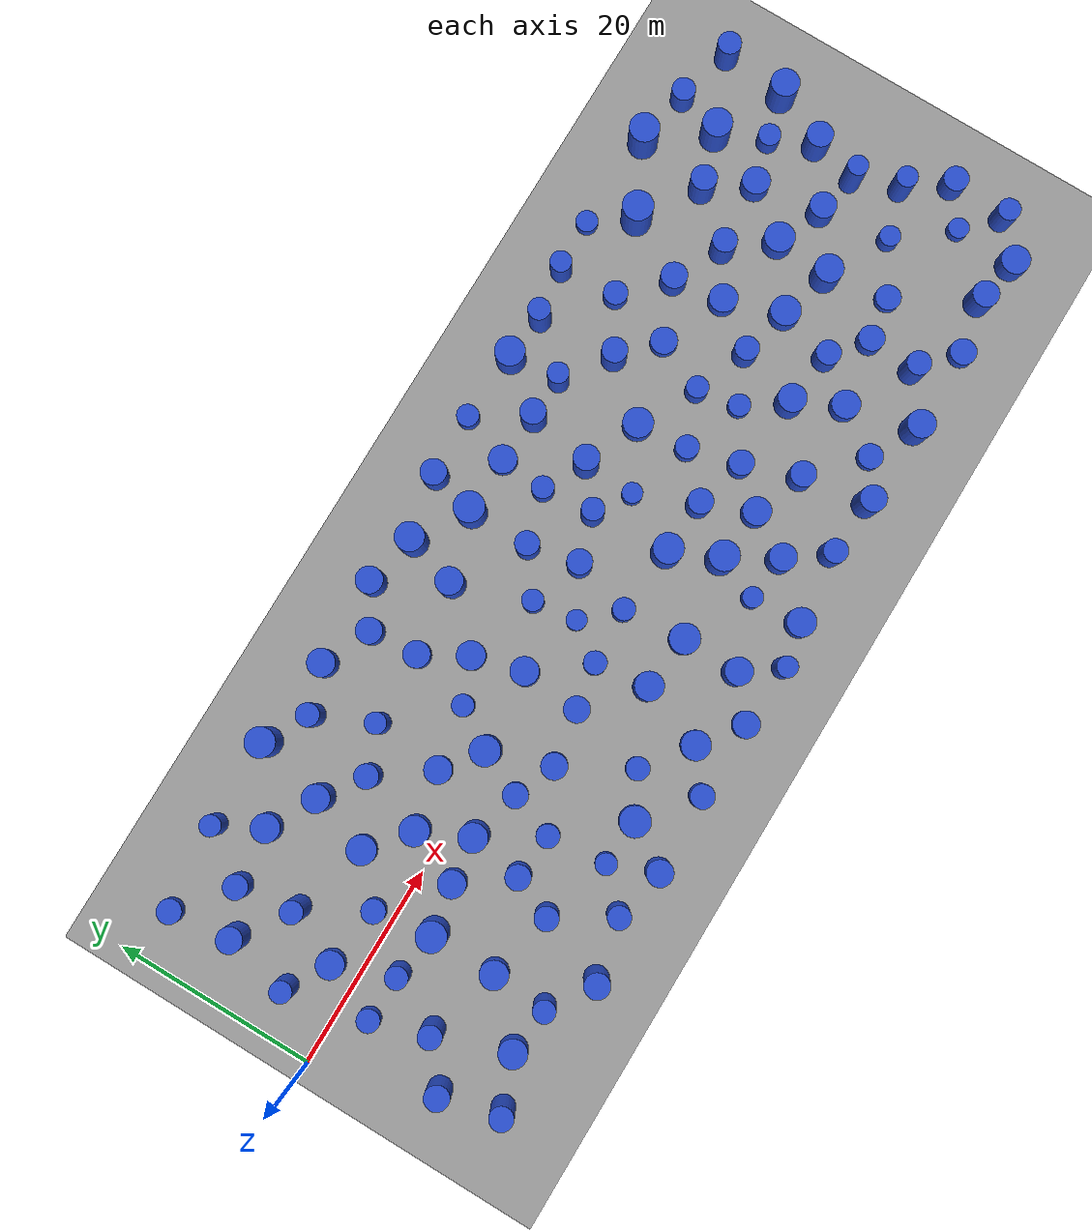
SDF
<sdf version="1.7">
 <world name="default">
  <plugin name="gazebo_ros_state" filename="libgazebo_ros_state.so">
   <ros>
    <namespace>/plug</namespace>
    <argument>model_states:=model_states_plug</argument>
    <argument>link_states:=link_states_plug</argument>
   </ros>
   <update_rate>100.0</update_rate>
  </plugin>
  <light name="light" type="directional">
   <pose>0 0 10 0 -0 0</pose>
   <diffuse>0.8 0.8 0.8 1</diffuse>
   <specular>0.2 0.2 0.2 1</specular>
   <attenuation>
    <range>1000</range>
    <constant>0.9</constant>
    <linear>0.01</linear>
    <quadratic>0.001</quadratic>
   </attenuation>
   <direction>-0.5 0.1 -0.9</direction>
   <spot><inner_angle>0</inner_angle><outer_angle>0</outer_angle><falloff>0</falloff></spot>
  </light>
  <gravity>0 0 -9.8</gravity>
  <magnetic_field>6e-06 2.3e-05 -4.2e-05</magnetic_field>
  <atmosphere type="adiabatic"/>
  <physics type="ode">
   <max_step_size>0.001</max_step_size>
   <real_time_factor>1</real_time_factor>
   <real_time_update_rate>1000</real_time_update_rate>
  </physics>
  <scene><ambient>0.4 0.4 0.4 1</ambient><background>0.7 0.7 0.7 1</background><shadows>1</shadows></scene>
  <audio><device>default</device></audio>
  <spherical_coordinates>
   <surface_model>EARTH_WGS84</surface_model>
   <latitude_deg>0</latitude_deg>
   <longitude_deg>0</longitude_deg>
   <elevation>0</elevation>
   <heading_deg>0</heading_deg>
  </spherical_coordinates>
  <model name="ground_plane_map">
   <static>1</static>
   <link name="link">
    <collision name="collision">
     <geometry><plane><normal>0 0 1</normal><size>110 50</size></plane></geometry>
     <surface>
      <contact><collide_without_contact>1</collide_without_contact></contact>
      <friction><ode><mu>100</mu><mu2>50</mu2></ode></friction>
     </surface>
    </collision>
    <visual name="visual">
     <cast_shadows>0</cast_shadows>
     <geometry><plane><normal>0 0 1</normal><size>110 50</size></plane></geometry>
     <material>
      <script><uri>file://media/materials/scripts/gazebo.material</uri><name>Gazebo/Grey</name></script>
     </material>
    </visual>
   </link>
   <pose>53 0 0 0 -0 0</pose>
  </model>
  <model name="0">
   <static>1</static>
   <link name="link">
    <inertial>
     <mass>2</mass>
     <inertia><ixx>4.14481</ixx><ixy>0</ixy><ixz>0</ixz><iyy>4.14481</iyy><iyz>0</iyz><izz>1.90158</izz></inertia>
    </inertial>
    <collision name="collision">
     <geometry><cylinder><length>4.37769</length><radius>1.37898</radius></cylinder></geometry>
     <surface><contact><collide_without_contact>1</collide_without_contact></contact></surface>
    </collision>
    <visual name="visual">
     <geometry><cylinder><length>4.37769</length><radius>1.37898</radius></cylinder></geometry>
     <material>
      <script><uri>file://media/materials/scripts/gazebo.material</uri><name>Gazebo/Blue</name></script>
     </material>
    </visual>
    <gravity>0</gravity>
   </link>
   <pose>45.2762 -8.97843 2.18884 0 -0 0</pose>
  </model>
  <model name="1">
   <static>1</static>
   <link name="link">
    <inertial>
     <mass>2</mass>
     <inertia><ixx>2.2684</ixx><ixy>0</ixy><ixz>0</ixz><iyy>2.2684</iyy><iyz>0</iyz><izz>1.44593</izz></inertia>
    </inertial>
    <collision name="collision">
     <geometry><cylinder><length>3.0451</length><radius>1.20247</radius></cylinder></geometry>
     <surface><contact><collide_without_contact>1</collide_without_contact></contact></surface>
    </collision>
    <visual name="visual">
     <geometry><cylinder><length>3.0451</length><radius>1.20247</radius></cylinder></geometry>
     <material>
      <script><uri>file://media/materials/scripts/gazebo.material</uri><name>Gazebo/Blue</name></script>
     </material>
    </visual>
    <gravity>0</gravity>
   </link>
   <pose>80.6973 -7.39447 1.52255 0 -0 0</pose>
  </model>
  <model name="2">
   <static>1</static>
   <link name="link">
    <inertial>
     <mass>2</mass>
     <inertia><ixx>2.24208</ixx><ixy>0</ixy><ixz>0</ixz><iyy>2.24208</iyy><iyz>0</iyz><izz>1.66847</izz></inertia>
    </inertial>
    <collision name="collision">
     <geometry><cylinder><length>2.90639</length><radius>1.29169</radius></cylinder></geometry>
     <surface><contact><collide_without_contact>1</collide_without_contact></contact></surface>
    </collision>
    <visual name="visual">
     <geometry><cylinder><length>2.90639</length><radius>1.29169</radius></cylinder></geometry>
     <material>
      <script><uri>file://media/materials/scripts/gazebo.material</uri><name>Gazebo/Blue</name></script>
     </material>
    </visual>
    <gravity>0</gravity>
   </link>
   <pose>92.757 0.175366 1.45319 0 -0 0</pose>
  </model>
  <model name="3">
   <static>1</static>
   <link name="link">
    <inertial>
     <mass>2</mass>
     <inertia><ixx>1.70358</ixx><ixy>0</ixy><ixz>0</ixz><iyy>1.70358</iyy><iyz>0</iyz><izz>1.89861</izz></inertia>
    </inertial>
    <collision name="collision">
     <geometry><cylinder><length>2.12735</length><radius>1.3779</radius></cylinder></geometry>
     <surface><contact><collide_without_contact>1</collide_without_contact></contact></surface>
    </collision>
    <visual name="visual">
     <geometry><cylinder><length>2.12735</length><radius>1.3779</radius></cylinder></geometry>
     <material>
      <script><uri>file://media/materials/scripts/gazebo.material</uri><name>Gazebo/Blue</name></script>
     </material>
    </visual>
    <gravity>0</gravity>
   </link>
   <pose>64.5107 -9.29219 1.06368 0 -0 0</pose>
  </model>
  <model name="4">
   <static>1</static>
   <link name="link">
    <inertial>
     <mass>2</mass>
     <inertia><ixx>4.69882</ixx><ixy>0</ixy><ixz>0</ixz><iyy>4.69882</iyy><iyz>0</iyz><izz>2.22425</izz></inertia>
    </inertial>
    <collision name="collision">
     <geometry><cylinder><length>4.63899</length><radius>1.49139</radius></cylinder></geometry>
     <surface><contact><collide_without_contact>1</collide_without_contact></contact></surface>
    </collision>
    <visual name="visual">
     <geometry><cylinder><length>4.63899</length><radius>1.49139</radius></cylinder></geometry>
     <material>
      <script><uri>file://media/materials/scripts/gazebo.material</uri><name>Gazebo/Blue</name></script>
     </material>
    </visual>
    <gravity>0</gravity>
   </link>
   <pose>83.0964 14.8871 2.31949 0 -0 0</pose>
  </model>
  <model name="5">
   <static>1</static>
   <link name="link">
    <inertial>
     <mass>2</mass>
     <inertia><ixx>1.76821</ixx><ixy>0</ixy><ixz>0</ixz><iyy>1.76821</iyy><iyz>0</iyz><izz>1.863</izz></inertia>
    </inertial>
    <collision name="collision">
     <geometry><cylinder><length>2.24059</length><radius>1.36492</radius></cylinder></geometry>
     <surface><contact><collide_without_contact>1</collide_without_contact></contact></surface>
    </collision>
    <visual name="visual">
     <geometry><cylinder><length>2.24059</length><radius>1.36492</radius></cylinder></geometry>
     <material>
      <script><uri>file://media/materials/scripts/gazebo.material</uri><name>Gazebo/Blue</name></script>
     </material>
    </visual>
    <gravity>0</gravity>
   </link>
   <pose>91.7951 6.85711 1.1203 0 -0 0</pose>
  </model>
  <model name="6">
   <static>1</static>
   <link name="link">
    <inertial>
     <mass>2</mass>
     <inertia><ixx>1.94226</ixx><ixy>0</ixy><ixz>0</ixz><iyy>1.94226</iyy><iyz>0</iyz><izz>1.10324</izz></inertia>
    </inertial>
    <collision name="collision">
     <geometry><cylinder><length>2.88857</length><radius>1.05035</radius></cylinder></geometry>
     <surface><contact><collide_without_contact>1</collide_without_contact></contact></surface>
    </collision>
    <visual name="visual">
     <geometry><cylinder><length>2.88857</length><radius>1.05035</radius></cylinder></geometry>
     <material>
      <script><uri>file://media/materials/scripts/gazebo.material</uri><name>Gazebo/Blue</name></script>
     </material>
    </visual>
    <gravity>0</gravity>
   </link>
   <pose>46.5555 4.20254 1.44429 0 -0 0</pose>
  </model>
  <model name="7">
   <static>1</static>
   <link name="link">
    <inertial>
     <mass>2</mass>
     <inertia><ixx>4.70701</ixx><ixy>0</ixy><ixz>0</ixz><iyy>4.70701</iyy><iyz>0</iyz><izz>2.20019</izz></inertia>
    </inertial>
    <collision name="collision">
     <geometry><cylinder><length>4.65204</length><radius>1.4833</radius></cylinder></geometry>
     <surface><contact><collide_without_contact>1</collide_without_contact></contact></surface>
    </collision>
    <visual name="visual">
     <geometry><cylinder><length>4.65204</length><radius>1.4833</radius></cylinder></geometry>
     <material>
      <script><uri>file://media/materials/scripts/gazebo.material</uri><name>Gazebo/Blue</name></script>
     </material>
    </visual>
    <gravity>0</gravity>
   </link>
   <pose>50.7692 13.5287 2.32602 0 -0 0</pose>
  </model>
  <model name="8">
   <static>1</static>
   <link name="link">
    <inertial>
     <mass>2</mass>
     <inertia><ixx>1.67846</ixx><ixy>0</ixy><ixz>0</ixz><iyy>1.67846</iyy><iyz>0</iyz><izz>1.96705</izz></inertia>
    </inertial>
    <collision name="collision">
     <geometry><cylinder><length>2.04197</length><radius>1.40251</radius></cylinder></geometry>
     <surface><contact><collide_without_contact>1</collide_without_contact></contact></surface>
    </collision>
    <visual name="visual">
     <geometry><cylinder><length>2.04197</length><radius>1.40251</radius></cylinder></geometry>
     <material>
      <script><uri>file://media/materials/scripts/gazebo.material</uri><name>Gazebo/Blue</name></script>
     </material>
    </visual>
    <gravity>0</gravity>
   </link>
   <pose>57.7333 -18.0752 1.02099 0 -0 0</pose>
  </model>
  <model name="9">
   <static>1</static>
   <link name="link">
    <inertial>
     <mass>2</mass>
     <inertia><ixx>3.22683</ixx><ixy>0</ixy><ixz>0</ixz><iyy>3.22683</iyy><iyz>0</iyz><izz>1.43859</izz></inertia>
    </inertial>
    <collision name="collision">
     <geometry><cylinder><length>3.87882</length><radius>1.19941</radius></cylinder></geometry>
     <surface><contact><collide_without_contact>1</collide_without_contact></contact></surface>
    </collision>
    <visual name="visual">
     <geometry><cylinder><length>3.87882</length><radius>1.19941</radius></cylinder></geometry>
     <material>
      <script><uri>file://media/materials/scripts/gazebo.material</uri><name>Gazebo/Blue</name></script>
     </material>
    </visual>
    <gravity>0</gravity>
   </link>
   <pose>84.7053 6.32276 1.93941 0 -0 0</pose>
  </model>
  <model name="10">
   <static>1</static>
   <link name="link">
    <inertial>
     <mass>2</mass>
     <inertia>
      <ixx>0.945435</ixx>
      <ixy>0</ixy>
      <ixz>0</ixz>
      <iyy>0.945435</iyy>
      <iyz>0</iyz>
      <izz>1.55448</izz>
     </inertia>
    </inertial>
    <collision name="collision">
     <geometry><cylinder><length>1.00457</length><radius>1.24679</radius></cylinder></geometry>
     <surface><contact><collide_without_contact>1</collide_without_contact></contact></surface>
    </collision>
    <visual name="visual">
     <geometry><cylinder><length>1.00457</length><radius>1.24679</radius></cylinder></geometry>
     <material>
      <script><uri>file://media/materials/scripts/gazebo.material</uri><name>Gazebo/Blue</name></script>
     </material>
    </visual>
    <gravity>0</gravity>
   </link>
   <pose>88.8436 -9.60499 0.502286 0 -0 0</pose>
  </model>
  <model name="11">
   <static>1</static>
   <link name="link">
    <inertial>
     <mass>2</mass>
     <inertia><ixx>1.91224</ixx><ixy>0</ixy><ixz>0</ixz><iyy>1.91224</iyy><iyz>0</iyz><izz>2.0599</izz></inertia>
    </inertial>
    <collision name="collision">
     <geometry><cylinder><length>2.30082</length><radius>1.43524</radius></cylinder></geometry>
     <surface><contact><collide_without_contact>1</collide_without_contact></contact></surface>
    </collision>
    <visual name="visual">
     <geometry><cylinder><length>2.30082</length><radius>1.43524</radius></cylinder></geometry>
     <material>
      <script><uri>file://media/materials/scripts/gazebo.material</uri><name>Gazebo/Blue</name></script>
     </material>
    </visual>
    <gravity>0</gravity>
   </link>
   <pose>22.9935 2.50664 1.15041 0 -0 0</pose>
  </model>
  <model name="12">
   <static>1</static>
   <link name="link">
    <inertial>
     <mass>2</mass>
     <inertia><ixx>1.73744</ixx><ixy>0</ixy><ixz>0</ixz><iyy>1.73744</iyy><iyz>0</iyz><izz>2.20157</izz></inertia>
    </inertial>
    <collision name="collision">
     <geometry><cylinder><length>1.95446</length><radius>1.48377</radius></cylinder></geometry>
     <surface><contact><collide_without_contact>1</collide_without_contact></contact></surface>
    </collision>
    <visual name="visual">
     <geometry><cylinder><length>1.95446</length><radius>1.48377</radius></cylinder></geometry>
     <material>
      <script><uri>file://media/materials/scripts/gazebo.material</uri><name>Gazebo/Blue</name></script>
     </material>
    </visual>
    <gravity>0</gravity>
   </link>
   <pose>82.4183 -1.92681 0.977232 0 -0 0</pose>
  </model>
  <model name="13">
   <static>1</static>
   <link name="link">
    <inertial>
     <mass>2</mass>
     <inertia>
      <ixx>0.964017</ixx>
      <ixy>0</ixy>
      <ixz>0</ixz>
      <iyy>0.964017</iyy>
      <iyz>0</iyz>
      <izz>1.34566</izz>
     </inertia>
    </inertial>
    <collision name="collision">
     <geometry><cylinder><length>1.32178</length><radius>1.16003</radius></cylinder></geometry>
     <surface><contact><collide_without_contact>1</collide_without_contact></contact></surface>
    </collision>
    <visual name="visual">
     <geometry><cylinder><length>1.32178</length><radius>1.16003</radius></cylinder></geometry>
     <material>
      <script><uri>file://media/materials/scripts/gazebo.material</uri><name>Gazebo/Blue</name></script>
     </material>
    </visual>
    <gravity>0</gravity>
   </link>
   <pose>14.8128 1.93175 0.660892 0 -0 0</pose>
  </model>
  <model name="14">
   <static>1</static>
   <link name="link">
    <inertial>
     <mass>2</mass>
     <inertia><ixx>3.25121</ixx><ixy>0</ixy><ixz>0</ixz><iyy>3.25121</iyy><iyz>0</iyz><izz>1.62236</izz></inertia>
    </inertial>
    <collision name="collision">
     <geometry><cylinder><length>3.82625</length><radius>1.27372</radius></cylinder></geometry>
     <surface><contact><collide_without_contact>1</collide_without_contact></contact></surface>
    </collision>
    <visual name="visual">
     <geometry><cylinder><length>3.82625</length><radius>1.27372</radius></cylinder></geometry>
     <material>
      <script><uri>file://media/materials/scripts/gazebo.material</uri><name>Gazebo/Blue</name></script>
     </material>
    </visual>
    <gravity>0</gravity>
   </link>
   <pose>98.2023 3.86457 1.91312 0 -0 0</pose>
  </model>
  <model name="15">
   <static>1</static>
   <link name="link">
    <inertial>
     <mass>2</mass>
     <inertia><ixx>2.61819</ixx><ixy>0</ixy><ixz>0</ixz><iyy>2.61819</iyy><iyz>0</iyz><izz>1.49449</izz></inertia>
    </inertial>
    <collision name="collision">
     <geometry><cylinder><length>3.35047</length><radius>1.22249</radius></cylinder></geometry>
     <surface><contact><collide_without_contact>1</collide_without_contact></contact></surface>
    </collision>
    <visual name="visual">
     <geometry><cylinder><length>3.35047</length><radius>1.22249</radius></cylinder></geometry>
     <material>
      <script><uri>file://media/materials/scripts/gazebo.material</uri><name>Gazebo/Blue</name></script>
     </material>
    </visual>
    <gravity>0</gravity>
   </link>
   <pose>62.3933 -4.32254 1.67523 0 -0 0</pose>
  </model>
  <model name="16">
   <static>1</static>
   <link name="link">
    <inertial>
     <mass>2</mass>
     <inertia><ixx>2.47357</ixx><ixy>0</ixy><ixz>0</ixz><iyy>2.47357</iyy><iyz>0</iyz><izz>1.3114</izz></inertia>
    </inertial>
    <collision name="collision">
     <geometry><cylinder><length>3.3026</length><radius>1.14516</radius></cylinder></geometry>
     <surface><contact><collide_without_contact>1</collide_without_contact></contact></surface>
    </collision>
    <visual name="visual">
     <geometry><cylinder><length>3.3026</length><radius>1.14516</radius></cylinder></geometry>
     <material>
      <script><uri>file://media/materials/scripts/gazebo.material</uri><name>Gazebo/Blue</name></script>
     </material>
    </visual>
    <gravity>0</gravity>
   </link>
   <pose>22.6505 -11.8133 1.6513 0 -0 0</pose>
  </model>
  <model name="17">
   <static>1</static>
   <link name="link">
    <inertial>
     <mass>2</mass>
     <inertia><ixx>2.86724</ixx><ixy>0</ixy><ixz>0</ixz><iyy>2.86724</iyy><iyz>0</iyz><izz>1.76446</izz></inertia>
    </inertial>
    <collision name="collision">
     <geometry><cylinder><length>3.45109</length><radius>1.32833</radius></cylinder></geometry>
     <surface><contact><collide_without_contact>1</collide_without_contact></contact></surface>
    </collision>
    <visual name="visual">
     <geometry><cylinder><length>3.45109</length><radius>1.32833</radius></cylinder></geometry>
     <material>
      <script><uri>file://media/materials/scripts/gazebo.material</uri><name>Gazebo/Blue</name></script>
     </material>
    </visual>
    <gravity>0</gravity>
   </link>
   <pose>50.7154 -15.3173 1.72555 0 -0 0</pose>
  </model>
  <model name="18">
   <static>1</static>
   <link name="link">
    <inertial>
     <mass>2</mass>
     <inertia><ixx>3.74185</ixx><ixy>0</ixy><ixz>0</ixz><iyy>3.74185</iyy><iyz>0</iyz><izz>2.06895</izz></inertia>
    </inertial>
    <collision name="collision">
     <geometry><cylinder><length>4.03042</length><radius>1.43839</radius></cylinder></geometry>
     <surface><contact><collide_without_contact>1</collide_without_contact></contact></surface>
    </collision>
    <visual name="visual">
     <geometry><cylinder><length>4.03042</length><radius>1.43839</radius></cylinder></geometry>
     <material>
      <script><uri>file://media/materials/scripts/gazebo.material</uri><name>Gazebo/Blue</name></script>
     </material>
    </visual>
    <gravity>0</gravity>
   </link>
   <pose>94.1201 12.7132 2.01521 0 -0 0</pose>
  </model>
  <model name="19">
   <static>1</static>
   <link name="link">
    <inertial>
     <mass>2</mass>
     <inertia><ixx>4.58352</ixx><ixy>0</ixy><ixz>0</ixz><iyy>4.58352</iyy><iyz>0</iyz><izz>2.1361</izz></inertia>
    </inertial>
    <collision name="collision">
     <geometry><cylinder><length>4.59269</length><radius>1.46154</radius></cylinder></geometry>
     <surface><contact><collide_without_contact>1</collide_without_contact></contact></surface>
    </collision>
    <visual name="visual">
     <geometry><cylinder><length>4.59269</length><radius>1.46154</radius></cylinder></geometry>
     <material>
      <script><uri>file://media/materials/scripts/gazebo.material</uri><name>Gazebo/Blue</name></script>
     </material>
    </visual>
    <gravity>0</gravity>
   </link>
   <pose>56.9413 -4.03041 2.29635 0 -0 0</pose>
  </model>
  <model name="20">
   <static>1</static>
   <link name="link">
    <inertial>
     <mass>2</mass>
     <inertia><ixx>3.08082</ixx><ixy>0</ixy><ixz>0</ixz><iyy>3.08082</iyy><iyz>0</iyz><izz>1.29463</izz></inertia>
    </inertial>
    <collision name="collision">
     <geometry><cylinder><length>3.82113</length><radius>1.13782</radius></cylinder></geometry>
     <surface><contact><collide_without_contact>1</collide_without_contact></contact></surface>
    </collision>
    <visual name="visual">
     <geometry><cylinder><length>3.82113</length><radius>1.13782</radius></cylinder></geometry>
     <material>
      <script><uri>file://media/materials/scripts/gazebo.material</uri><name>Gazebo/Blue</name></script>
     </material>
    </visual>
    <gravity>0</gravity>
   </link>
   <pose>101.496 15.7288 1.91057 0 -0 0</pose>
  </model>
  <model name="21">
   <static>1</static>
   <link name="link">
    <inertial>
     <mass>2</mass>
     <inertia><ixx>3.44477</ixx><ixy>0</ixy><ixz>0</ixz><iyy>3.44477</iyy><iyz>0</iyz><izz>1.08407</izz></inertia>
    </inertial>
    <collision name="collision">
     <geometry><cylinder><length>4.1733</length><radius>1.04119</radius></cylinder></geometry>
     <surface><contact><collide_without_contact>1</collide_without_contact></contact></surface>
    </collision>
    <visual name="visual">
     <geometry><cylinder><length>4.1733</length><radius>1.04119</radius></cylinder></geometry>
     <material>
      <script><uri>file://media/materials/scripts/gazebo.material</uri><name>Gazebo/Blue</name></script>
     </material>
    </visual>
    <gravity>0</gravity>
   </link>
   <pose>65.7437 13.0845 2.08665 0 -0 0</pose>
  </model>
  <model name="22">
   <static>1</static>
   <link name="link">
    <inertial>
     <mass>2</mass>
     <inertia><ixx>1.58085</ixx><ixy>0</ixy><ixz>0</ixz><iyy>1.58085</iyy><iyz>0</iyz><izz>1.86526</izz></inertia>
    </inertial>
    <collision name="collision">
     <geometry><cylinder><length>1.97214</length><radius>1.36574</radius></cylinder></geometry>
     <surface><contact><collide_without_contact>1</collide_without_contact></contact></surface>
    </collision>
    <visual name="visual">
     <geometry><cylinder><length>1.97214</length><radius>1.36574</radius></cylinder></geometry>
     <material>
      <script><uri>file://media/materials/scripts/gazebo.material</uri><name>Gazebo/Blue</name></script>
     </material>
    </visual>
    <gravity>0</gravity>
   </link>
   <pose>15.7592 -10.418 0.986071 0 -0 0</pose>
  </model>
  <model name="23">
   <static>1</static>
   <link name="link">
    <inertial>
     <mass>2</mass>
     <inertia><ixx>3.58983</ixx><ixy>0</ixy><ixz>0</ixz><iyy>3.58983</iyy><iyz>0</iyz><izz>1.36018</izz></inertia>
    </inertial>
    <collision name="collision">
     <geometry><cylinder><length>4.17833</length><radius>1.16627</radius></cylinder></geometry>
     <surface><contact><collide_without_contact>1</collide_without_contact></contact></surface>
    </collision>
    <visual name="visual">
     <geometry><cylinder><length>4.17833</length><radius>1.16627</radius></cylinder></geometry>
     <material>
      <script><uri>file://media/materials/scripts/gazebo.material</uri><name>Gazebo/Blue</name></script>
     </material>
    </visual>
    <gravity>0</gravity>
   </link>
   <pose>83.8544 -15.0441 2.08917 0 -0 0</pose>
  </model>
  <model name="24">
   <static>1</static>
   <link name="link">
    <inertial>
     <mass>2</mass>
     <inertia><ixx>1.32861</ixx><ixy>0</ixy><ixz>0</ixz><iyy>1.32861</iyy><iyz>0</iyz><izz>1.81936</izz></inertia>
    </inertial>
    <collision name="collision">
     <geometry><cylinder><length>1.58543</length><radius>1.34884</radius></cylinder></geometry>
     <surface><contact><collide_without_contact>1</collide_without_contact></contact></surface>
    </collision>
    <visual name="visual">
     <geometry><cylinder><length>1.58543</length><radius>1.34884</radius></cylinder></geometry>
     <material>
      <script><uri>file://media/materials/scripts/gazebo.material</uri><name>Gazebo/Blue</name></script>
     </material>
    </visual>
    <gravity>0</gravity>
   </link>
   <pose>8.75022 2.75537 0.792717 0 -0 0</pose>
  </model>
  <model name="25">
   <static>1</static>
   <link name="link">
    <inertial>
     <mass>2</mass>
     <inertia><ixx>4.39114</ixx><ixy>0</ixy><ixz>0</ixz><iyy>4.39114</iyy><iyz>0</iyz><izz>1.60554</izz></inertia>
    </inertial>
    <collision name="collision">
     <geometry><cylinder><length>4.64006</length><radius>1.2671</radius></cylinder></geometry>
     <surface><contact><collide_without_contact>1</collide_without_contact></contact></surface>
    </collision>
    <visual name="visual">
     <geometry><cylinder><length>4.64006</length><radius>1.2671</radius></cylinder></geometry>
     <material>
      <script><uri>file://media/materials/scripts/gazebo.material</uri><name>Gazebo/Blue</name></script>
     </material>
    </visual>
    <gravity>0</gravity>
   </link>
   <pose>70.6013 -17.7327 2.32003 0 -0 0</pose>
  </model>
  <model name="26">
   <static>1</static>
   <link name="link">
    <inertial>
     <mass>2</mass>
     <inertia><ixx>2.93772</ixx><ixy>0</ixy><ixz>0</ixz><iyy>2.93772</iyy><iyz>0</iyz><izz>1.69825</izz></inertia>
    </inertial>
    <collision name="collision">
     <geometry><cylinder><length>3.54</length><radius>1.30317</radius></cylinder></geometry>
     <surface><contact><collide_without_contact>1</collide_without_contact></contact></surface>
    </collision>
    <visual name="visual">
     <geometry><cylinder><length>3.54</length><radius>1.30317</radius></cylinder></geometry>
     <material>
      <script><uri>file://media/materials/scripts/gazebo.material</uri><name>Gazebo/Blue</name></script>
     </material>
    </visual>
    <gravity>0</gravity>
   </link>
   <pose>40.3525 17.9683 1.77 0 -0 0</pose>
  </model>
  <model name="27">
   <static>1</static>
   <link name="link">
    <inertial>
     <mass>2</mass>
     <inertia>
      <ixx>0.729598</ixx>
      <ixy>0</ixy>
      <ixz>0</ixz>
      <iyy>0.729598</iyy>
      <iyz>0</iyz>
      <izz>1.02175</izz>
     </inertia>
    </inertial>
    <collision name="collision">
     <geometry><cylinder><length>1.14557</length><radius>1.01082</radius></cylinder></geometry>
     <surface><contact><collide_without_contact>1</collide_without_contact></contact></surface>
    </collision>
    <visual name="visual">
     <geometry><cylinder><length>1.14557</length><radius>1.01082</radius></cylinder></geometry>
     <material>
      <script><uri>file://media/materials/scripts/gazebo.material</uri><name>Gazebo/Blue</name></script>
     </material>
    </visual>
    <gravity>0</gravity>
   </link>
   <pose>98.1711 -11.9642 0.572784 0 -0 0</pose>
  </model>
  <model name="28">
   <static>1</static>
   <link name="link">
    <inertial>
     <mass>2</mass>
     <inertia>
      <ixx>0.983625</ixx>
      <ixy>0</ixy>
      <ixz>0</ixz>
      <iyy>0.983625</iyy>
      <iyz>0</iyz>
      <izz>1.22166</izz>
     </inertia>
    </inertial>
    <collision name="collision">
     <geometry><cylinder><length>1.49558</length><radius>1.10529</radius></cylinder></geometry>
     <surface><contact><collide_without_contact>1</collide_without_contact></contact></surface>
    </collision>
    <visual name="visual">
     <geometry><cylinder><length>1.49558</length><radius>1.10529</radius></cylinder></geometry>
     <material>
      <script><uri>file://media/materials/scripts/gazebo.material</uri><name>Gazebo/Blue</name></script>
     </material>
    </visual>
    <gravity>0</gravity>
   </link>
   <pose>6.33318 -2.81082 0.74779 0 -0 0</pose>
  </model>
  <model name="29">
   <static>1</static>
   <link name="link">
    <inertial>
     <mass>2</mass>
     <inertia>
      <ixx>0.967878</ixx>
      <ixy>0</ixy>
      <ixz>0</ixz>
      <iyy>0.967878</iyy>
      <iyz>0</iyz>
      <izz>1.27681</izz>
     </inertia>
    </inertial>
    <collision name="collision">
     <geometry><cylinder><length>1.406</length><radius>1.12996</radius></cylinder></geometry>
     <surface><contact><collide_without_contact>1</collide_without_contact></contact></surface>
    </collision>
    <visual name="visual">
     <geometry><cylinder><length>1.406</length><radius>1.12996</radius></cylinder></geometry>
     <material>
      <script><uri>file://media/materials/scripts/gazebo.material</uri><name>Gazebo/Blue</name></script>
     </material>
    </visual>
    <gravity>0</gravity>
   </link>
   <pose>38.3677 -12.0648 0.703 0 -0 0</pose>
  </model>
  <model name="30">
   <static>1</static>
   <link name="link">
    <inertial>
     <mass>2</mass>
     <inertia><ixx>2.03446</ixx><ixy>0</ixy><ixz>0</ixz><iyy>2.03446</iyy><iyz>0</iyz><izz>1.03977</izz></inertia>
    </inertial>
    <collision name="collision">
     <geometry><cylinder><length>3.01455</length><radius>1.01969</radius></cylinder></geometry>
     <surface><contact><collide_without_contact>1</collide_without_contact></contact></surface>
    </collision>
    <visual name="visual">
     <geometry><cylinder><length>3.01455</length><radius>1.01969</radius></cylinder></geometry>
     <material>
      <script><uri>file://media/materials/scripts/gazebo.material</uri><name>Gazebo/Blue</name></script>
     </material>
    </visual>
    <gravity>0</gravity>
   </link>
   <pose>13.906 18.5337 1.50727 0 -0 0</pose>
  </model>
  <model name="31">
   <static>1</static>
   <link name="link">
    <inertial>
     <mass>2</mass>
     <inertia><ixx>1.2338</ixx><ixy>0</ixy><ixz>0</ixz><iyy>1.2338</iyy><iyz>0</iyz><izz>1.3907</izz></inertia>
    </inertial>
    <collision name="collision">
     <geometry><cylinder><length>1.79742</length><radius>1.17928</radius></cylinder></geometry>
     <surface><contact><collide_without_contact>1</collide_without_contact></contact></surface>
    </collision>
    <visual name="visual">
     <geometry><cylinder><length>1.79742</length><radius>1.17928</radius></cylinder></geometry>
     <material>
      <script><uri>file://media/materials/scripts/gazebo.material</uri><name>Gazebo/Blue</name></script>
     </material>
    </visual>
    <gravity>0</gravity>
   </link>
   <pose>75.6136 12.7351 0.898712 0 -0 0</pose>
  </model>
  <model name="32">
   <static>1</static>
   <link name="link">
    <inertial>
     <mass>2</mass>
     <inertia><ixx>4.22923</ixx><ixy>0</ixy><ixz>0</ixz><iyy>4.22923</iyy><iyz>0</iyz><izz>1.1766</izz></inertia>
    </inertial>
    <collision name="collision">
     <geometry><cylinder><length>4.67393</length><radius>1.08471</radius></cylinder></geometry>
     <surface><contact><collide_without_contact>1</collide_without_contact></contact></surface>
    </collision>
    <visual name="visual">
     <geometry><cylinder><length>4.67393</length><radius>1.08471</radius></cylinder></geometry>
     <material>
      <script><uri>file://media/materials/scripts/gazebo.material</uri><name>Gazebo/Blue</name></script>
     </material>
    </visual>
    <gravity>0</gravity>
   </link>
   <pose>69.8895 17.6498 2.33696 0 -0 0</pose>
  </model>
  <model name="33">
   <static>1</static>
   <link name="link">
    <inertial>
     <mass>2</mass>
     <inertia><ixx>1.14831</ixx><ixy>0</ixy><ixz>0</ixz><iyy>1.14831</iyy><iyz>0</iyz><izz>1.79051</izz></inertia>
    </inertial>
    <collision name="collision">
     <geometry><cylinder><length>1.2322</length><radius>1.3381</radius></cylinder></geometry>
     <surface><contact><collide_without_contact>1</collide_without_contact></contact></surface>
    </collision>
    <visual name="visual">
     <geometry><cylinder><length>1.2322</length><radius>1.3381</radius></cylinder></geometry>
     <material>
      <script><uri>file://media/materials/scripts/gazebo.material</uri><name>Gazebo/Blue</name></script>
     </material>
    </visual>
    <gravity>0</gravity>
   </link>
   <pose>28.7359 3.61262 0.616102 0 -0 0</pose>
  </model>
  <model name="34">
   <static>1</static>
   <link name="link">
    <inertial>
     <mass>2</mass>
     <inertia><ixx>1.86936</ixx><ixy>0</ixy><ixz>0</ixz><iyy>1.86936</iyy><iyz>0</iyz><izz>1.18246</izz></inertia>
    </inertial>
    <collision name="collision">
     <geometry><cylinder><length>2.76926</length><radius>1.08741</radius></cylinder></geometry>
     <surface><contact><collide_without_contact>1</collide_without_contact></contact></surface>
    </collision>
    <visual name="visual">
     <geometry><cylinder><length>2.76926</length><radius>1.08741</radius></cylinder></geometry>
     <material>
      <script><uri>file://media/materials/scripts/gazebo.material</uri><name>Gazebo/Blue</name></script>
     </material>
    </visual>
    <gravity>0</gravity>
   </link>
   <pose>50.2243 -3.40785 1.38463 0 -0 0</pose>
  </model>
  <model name="35">
   <static>1</static>
   <link name="link">
    <inertial>
     <mass>2</mass>
     <inertia><ixx>2.57582</ixx><ixy>0</ixy><ixz>0</ixz><iyy>2.57582</iyy><iyz>0</iyz><izz>1.57327</izz></inertia>
    </inertial>
    <collision name="collision">
     <geometry><cylinder><length>3.27645</length><radius>1.2543</radius></cylinder></geometry>
     <surface><contact><collide_without_contact>1</collide_without_contact></contact></surface>
    </collision>
    <visual name="visual">
     <geometry><cylinder><length>3.27645</length><radius>1.2543</radius></cylinder></geometry>
     <material>
      <script><uri>file://media/materials/scripts/gazebo.material</uri><name>Gazebo/Blue</name></script>
     </material>
    </visual>
    <gravity>0</gravity>
   </link>
   <pose>34.6176 -5.35558 1.63823 0 -0 0</pose>
  </model>
  <model name="36">
   <static>1</static>
   <link name="link">
    <inertial>
     <mass>2</mass>
     <inertia><ixx>3.78802</ixx><ixy>0</ixy><ixz>0</ixz><iyy>3.78802</iyy><iyz>0</iyz><izz>1.26667</izz></inertia>
    </inertial>
    <collision name="collision">
     <geometry><cylinder><length>4.35064</length><radius>1.12547</radius></cylinder></geometry>
     <surface><contact><collide_without_contact>1</collide_without_contact></contact></surface>
    </collision>
    <visual name="visual">
     <geometry><cylinder><length>4.35064</length><radius>1.12547</radius></cylinder></geometry>
     <material>
      <script><uri>file://media/materials/scripts/gazebo.material</uri><name>Gazebo/Blue</name></script>
     </material>
    </visual>
    <gravity>0</gravity>
   </link>
   <pose>8.59226 -8.27146 2.17532 0 -0 0</pose>
  </model>
  <model name="37">
   <static>1</static>
   <link name="link">
    <inertial>
     <mass>2</mass>
     <inertia><ixx>1.73073</ixx><ixy>0</ixy><ixz>0</ixz><iyy>1.73073</iyy><iyz>0</iyz><izz>2.18024</izz></inertia>
    </inertial>
    <collision name="collision">
     <geometry><cylinder><length>1.96052</length><radius>1.47656</radius></cylinder></geometry>
     <surface><contact><collide_without_contact>1</collide_without_contact></contact></surface>
    </collision>
    <visual name="visual">
     <geometry><cylinder><length>1.96052</length><radius>1.47656</radius></cylinder></geometry>
     <material>
      <script><uri>file://media/materials/scripts/gazebo.material</uri><name>Gazebo/Blue</name></script>
     </material>
    </visual>
    <gravity>0</gravity>
   </link>
   <pose>65.9798 4.48552 0.980261 0 -0 0</pose>
  </model>
  <model name="38">
   <static>1</static>
   <link name="link">
    <inertial>
     <mass>2</mass>
     <inertia><ixx>3.19928</ixx><ixy>0</ixy><ixz>0</ixz><iyy>3.19928</iyy><iyz>0</iyz><izz>1.42566</izz></inertia>
    </inertial>
    <collision name="collision">
     <geometry><cylinder><length>3.86248</length><radius>1.19401</radius></cylinder></geometry>
     <surface><contact><collide_without_contact>1</collide_without_contact></contact></surface>
    </collision>
    <visual name="visual">
     <geometry><cylinder><length>3.86248</length><radius>1.19401</radius></cylinder></geometry>
     <material>
      <script><uri>file://media/materials/scripts/gazebo.material</uri><name>Gazebo/Blue</name></script>
     </material>
    </visual>
    <gravity>0</gravity>
   </link>
   <pose>4.34279 -11.5728 1.93124 0 -0 0</pose>
  </model>
  <model name="39">
   <static>1</static>
   <link name="link">
    <inertial>
     <mass>2</mass>
     <inertia><ixx>1.53761</ixx><ixy>0</ixy><ixz>0</ixz><iyy>1.53761</iyy><iyz>0</iyz><izz>1.25375</izz></inertia>
    </inertial>
    <collision name="collision">
     <geometry><cylinder><length>2.33761</length><radius>1.11971</radius></cylinder></geometry>
     <surface><contact><collide_without_contact>1</collide_without_contact></contact></surface>
    </collision>
    <visual name="visual">
     <geometry><cylinder><length>2.33761</length><radius>1.11971</radius></cylinder></geometry>
     <material>
      <script><uri>file://media/materials/scripts/gazebo.material</uri><name>Gazebo/Blue</name></script>
     </material>
    </visual>
    <gravity>0</gravity>
   </link>
   <pose>44.6323 -3.69045 1.1688 0 -0 0</pose>
  </model>
  <model name="40">
   <static>1</static>
   <link name="link">
    <inertial>
     <mass>2</mass>
     <inertia><ixx>3.14692</ixx><ixy>0</ixy><ixz>0</ixz><iyy>3.14692</iyy><iyz>0</iyz><izz>1.46195</izz></inertia>
    </inertial>
    <collision name="collision">
     <geometry><cylinder><length>3.80732</length><radius>1.20911</radius></cylinder></geometry>
     <surface><contact><collide_without_contact>1</collide_without_contact></contact></surface>
    </collision>
    <visual name="visual">
     <geometry><cylinder><length>3.80732</length><radius>1.20911</radius></cylinder></geometry>
     <material>
      <script><uri>file://media/materials/scripts/gazebo.material</uri><name>Gazebo/Blue</name></script>
     </material>
    </visual>
    <gravity>0</gravity>
   </link>
   <pose>51.7574 2.30771 1.90366 0 -0 0</pose>
  </model>
  <model name="41">
   <static>1</static>
   <link name="link">
    <inertial>
     <mass>2</mass>
     <inertia><ixx>3.73559</ixx><ixy>0</ixy><ixz>0</ixz><iyy>3.73559</iyy><iyz>0</iyz><izz>2.07918</izz></inertia>
    </inertial>
    <collision name="collision">
     <geometry><cylinder><length>4.02194</length><radius>1.44194</radius></cylinder></geometry>
     <surface><contact><collide_without_contact>1</collide_without_contact></contact></surface>
    </collision>
    <visual name="visual">
     <geometry><cylinder><length>4.02194</length><radius>1.44194</radius></cylinder></geometry>
     <material>
      <script><uri>file://media/materials/scripts/gazebo.material</uri><name>Gazebo/Blue</name></script>
     </material>
    </visual>
    <gravity>0</gravity>
   </link>
   <pose>22.6999 18.5365 2.01097 0 -0 0</pose>
  </model>
  <model name="42">
   <static>1</static>
   <link name="link">
    <inertial>
     <mass>2</mass>
     <inertia><ixx>2.62219</ixx><ixy>0</ixy><ixz>0</ixz><iyy>2.62219</iyy><iyz>0</iyz><izz>1.08521</izz></inertia>
    </inertial>
    <collision name="collision">
     <geometry><cylinder><length>3.53236</length><radius>1.04173</radius></cylinder></geometry>
     <surface><contact><collide_without_contact>1</collide_without_contact></contact></surface>
    </collision>
    <visual name="visual">
     <geometry><cylinder><length>3.53236</length><radius>1.04173</radius></cylinder></geometry>
     <material>
      <script><uri>file://media/materials/scripts/gazebo.material</uri><name>Gazebo/Blue</name></script>
     </material>
    </visual>
    <gravity>0</gravity>
   </link>
   <pose>75.0855 18.4586 1.76618 0 -0 0</pose>
  </model>
  <model name="43">
   <static>1</static>
   <link name="link">
    <inertial>
     <mass>2</mass>
     <inertia><ixx>2.02978</ixx><ixy>0</ixy><ixz>0</ixz><iyy>2.02978</iyy><iyz>0</iyz><izz>1.79361</izz></inertia>
    </inertial>
    <collision name="collision">
     <geometry><cylinder><length>2.60727</length><radius>1.33926</radius></cylinder></geometry>
     <surface><contact><collide_without_contact>1</collide_without_contact></contact></surface>
    </collision>
    <visual name="visual">
     <geometry><cylinder><length>2.60727</length><radius>1.33926</radius></cylinder></geometry>
     <material>
      <script><uri>file://media/materials/scripts/gazebo.material</uri><name>Gazebo/Blue</name></script>
     </material>
    </visual>
    <gravity>0</gravity>
   </link>
   <pose>31.5876 17.8589 1.30363 0 -0 0</pose>
  </model>
  <model name="44">
   <static>1</static>
   <link name="link">
    <inertial>
     <mass>2</mass>
     <inertia><ixx>1.34512</ixx><ixy>0</ixy><ixz>0</ixz><iyy>1.34512</iyy><iyz>0</iyz><izz>2.03624</izz></inertia>
    </inertial>
    <collision name="collision">
     <geometry><cylinder><length>1.40072</length><radius>1.42697</radius></cylinder></geometry>
     <surface><contact><collide_without_contact>1</collide_without_contact></contact></surface>
    </collision>
    <visual name="visual">
     <geometry><cylinder><length>1.40072</length><radius>1.42697</radius></cylinder></geometry>
     <material>
      <script><uri>file://media/materials/scripts/gazebo.material</uri><name>Gazebo/Blue</name></script>
     </material>
    </visual>
    <gravity>0</gravity>
   </link>
   <pose>42.9644 -15.5514 0.700361 0 -0 0</pose>
  </model>
  <model name="45">
   <static>1</static>
   <link name="link">
    <inertial>
     <mass>2</mass>
     <inertia><ixx>1.48634</ixx><ixy>0</ixy><ixz>0</ixz><iyy>1.48634</iyy><iyz>0</iyz><izz>1.50428</izz></inertia>
    </inertial>
    <collision name="collision">
     <geometry><cylinder><length>2.09886</length><radius>1.22649</radius></cylinder></geometry>
     <surface><contact><collide_without_contact>1</collide_without_contact></contact></surface>
    </collision>
    <visual name="visual">
     <geometry><cylinder><length>2.09886</length><radius>1.22649</radius></cylinder></geometry>
     <material>
      <script><uri>file://media/materials/scripts/gazebo.material</uri><name>Gazebo/Blue</name></script>
     </material>
    </visual>
    <gravity>0</gravity>
   </link>
   <pose>67.7085 -5.7427 1.04943 0 -0 0</pose>
  </model>
  <model name="46">
   <static>1</static>
   <link name="link">
    <inertial>
     <mass>2</mass>
     <inertia><ixx>4.0051</ixx><ixy>0</ixy><ixz>0</ixz><iyy>4.0051</iyy><iyz>0</iyz><izz>1.29779</izz></inertia>
    </inertial>
    <collision name="collision">
     <geometry><cylinder><length>4.48746</length><radius>1.1392</radius></cylinder></geometry>
     <surface><contact><collide_without_contact>1</collide_without_contact></contact></surface>
    </collision>
    <visual name="visual">
     <geometry><cylinder><length>4.48746</length><radius>1.1392</radius></cylinder></geometry>
     <material>
      <script><uri>file://media/materials/scripts/gazebo.material</uri><name>Gazebo/Blue</name></script>
     </material>
    </visual>
    <gravity>0</gravity>
   </link>
   <pose>5.95432 -17.3269 2.24373 0 -0 0</pose>
  </model>
  <model name="47">
   <static>1</static>
   <link name="link">
    <inertial>
     <mass>2</mass>
     <inertia><ixx>3.12949</ixx><ixy>0</ixy><ixz>0</ixz><iyy>3.12949</iyy><iyz>0</iyz><izz>1.6363</izz></inertia>
    </inertial>
    <collision name="collision">
     <geometry><cylinder><length>3.72399</length><radius>1.27918</radius></cylinder></geometry>
     <surface><contact><collide_without_contact>1</collide_without_contact></contact></surface>
    </collision>
    <visual name="visual">
     <geometry><cylinder><length>3.72399</length><radius>1.27918</radius></cylinder></geometry>
     <material>
      <script><uri>file://media/materials/scripts/gazebo.material</uri><name>Gazebo/Blue</name></script>
     </material>
    </visual>
    <gravity>0</gravity>
   </link>
   <pose>92.9366 -17.1481 1.86199 0 -0 0</pose>
  </model>
  <model name="48">
   <static>1</static>
   <link name="link">
    <inertial>
     <mass>2</mass>
     <inertia><ixx>3.5742</ixx><ixy>0</ixy><ixz>0</ixz><iyy>3.5742</iyy><iyz>0</iyz><izz>1.82429</izz></inertia>
    </inertial>
    <collision name="collision">
     <geometry><cylinder><length>3.99654</length><radius>1.35066</radius></cylinder></geometry>
     <surface><contact><collide_without_contact>1</collide_without_contact></contact></surface>
    </collision>
    <visual name="visual">
     <geometry><cylinder><length>3.99654</length><radius>1.35066</radius></cylinder></geometry>
     <material>
      <script><uri>file://media/materials/scripts/gazebo.material</uri><name>Gazebo/Blue</name></script>
     </material>
    </visual>
    <gravity>0</gravity>
   </link>
   <pose>40.5895 1.41469 1.99827 0 -0 0</pose>
  </model>
  <model name="49">
   <static>1</static>
   <link name="link">
    <inertial>
     <mass>2</mass>
     <inertia><ixx>1.39564</ixx><ixy>0</ixy><ixz>0</ixz><iyy>1.39564</iyy><iyz>0</iyz><izz>1.6733</izz></inertia>
    </inertial>
    <collision name="collision">
     <geometry><cylinder><length>1.83138</length><radius>1.29356</radius></cylinder></geometry>
     <surface><contact><collide_without_contact>1</collide_without_contact></contact></surface>
    </collision>
    <visual name="visual">
     <geometry><cylinder><length>1.83138</length><radius>1.29356</radius></cylinder></geometry>
     <material>
      <script><uri>file://media/materials/scripts/gazebo.material</uri><name>Gazebo/Blue</name></script>
     </material>
    </visual>
    <gravity>0</gravity>
   </link>
   <pose>36.7718 10.8356 0.915688 0 -0 0</pose>
  </model>
  <model name="50">
   <static>1</static>
   <link name="link">
    <inertial>
     <mass>2</mass>
     <inertia><ixx>3.18474</ixx><ixy>0</ixy><ixz>0</ixz><iyy>3.18474</iyy><iyz>0</iyz><izz>1.36686</izz></inertia>
    </inertial>
    <collision name="collision">
     <geometry><cylinder><length>3.874</length><radius>1.16913</radius></cylinder></geometry>
     <surface><contact><collide_without_contact>1</collide_without_contact></contact></surface>
    </collision>
    <visual name="visual">
     <geometry><cylinder><length>3.874</length><radius>1.16913</radius></cylinder></geometry>
     <material>
      <script><uri>file://media/materials/scripts/gazebo.material</uri><name>Gazebo/Blue</name></script>
     </material>
    </visual>
    <gravity>0</gravity>
   </link>
   <pose>64.772 -17.2791 1.937 0 -0 0</pose>
  </model>
  <model name="51">
   <static>1</static>
   <link name="link">
    <inertial>
     <mass>2</mass>
     <inertia><ixx>1.56822</ixx><ixy>0</ixy><ixz>0</ixz><iyy>1.56822</iyy><iyz>0</iyz><izz>2.22295</izz></inertia>
    </inertial>
    <collision name="collision">
     <geometry><cylinder><length>1.65544</length><radius>1.49096</radius></cylinder></geometry>
     <surface><contact><collide_without_contact>1</collide_without_contact></contact></surface>
    </collision>
    <visual name="visual">
     <geometry><cylinder><length>1.65544</length><radius>1.49096</radius></cylinder></geometry>
     <material>
      <script><uri>file://media/materials/scripts/gazebo.material</uri><name>Gazebo/Blue</name></script>
     </material>
    </visual>
    <gravity>0</gravity>
   </link>
   <pose>50.8719 -9.63558 0.827721 0 -0 0</pose>
  </model>
  <model name="52">
   <static>1</static>
   <link name="link">
    <inertial>
     <mass>2</mass>
     <inertia>
      <ixx>0.831043</ixx>
      <ixy>0</ixy>
      <ixz>0</ixz>
      <iyy>0.831043</iyy>
      <iyz>0</iyz>
      <izz>1.18765</izz>
     </inertia>
    </inertial>
    <collision name="collision">
     <geometry><cylinder><length>1.19303</length><radius>1.08979</radius></cylinder></geometry>
     <surface><contact><collide_without_contact>1</collide_without_contact></contact></surface>
    </collision>
    <visual name="visual">
     <geometry><cylinder><length>1.19303</length><radius>1.08979</radius></cylinder></geometry>
     <material>
      <script><uri>file://media/materials/scripts/gazebo.material</uri><name>Gazebo/Blue</name></script>
     </material>
    </visual>
    <gravity>0</gravity>
   </link>
   <pose>72.5245 -2.77846 0.596513 0 -0 0</pose>
  </model>
  <model name="53">
   <static>1</static>
   <link name="link">
    <inertial>
     <mass>2</mass>
     <inertia><ixx>1.74712</ixx><ixy>0</ixy><ixz>0</ixz><iyy>1.74712</iyy><iyz>0</iyz><izz>1.86972</izz></inertia>
    </inertial>
    <collision name="collision">
     <geometry><cylinder><length>2.20761</length><radius>1.36738</radius></cylinder></geometry>
     <surface><contact><collide_without_contact>1</collide_without_contact></contact></surface>
    </collision>
    <visual name="visual">
     <geometry><cylinder><length>2.20761</length><radius>1.36738</radius></cylinder></geometry>
     <material>
      <script><uri>file://media/materials/scripts/gazebo.material</uri><name>Gazebo/Blue</name></script>
     </material>
    </visual>
    <gravity>0</gravity>
   </link>
   <pose>10.7708 -15.4774 1.10381 0 -0 0</pose>
  </model>
  <model name="54">
   <static>1</static>
   <link name="link">
    <inertial>
     <mass>2</mass>
     <inertia><ixx>3.19702</ixx><ixy>0</ixy><ixz>0</ixz><iyy>3.19702</iyy><iyz>0</iyz><izz>1.06209</izz></inertia>
    </inertial>
    <collision name="collision">
     <geometry><cylinder><length>3.99948</length><radius>1.03058</radius></cylinder></geometry>
     <surface><contact><collide_without_contact>1</collide_without_contact></contact></surface>
    </collision>
    <visual name="visual">
     <geometry><cylinder><length>3.99948</length><radius>1.03058</radius></cylinder></geometry>
     <material>
      <script><uri>file://media/materials/scripts/gazebo.material</uri><name>Gazebo/Blue</name></script>
     </material>
    </visual>
    <gravity>0</gravity>
   </link>
   <pose>29.5844 10.5129 1.99974 0 -0 0</pose>
  </model>
  <model name="55">
   <static>1</static>
   <link name="link">
    <inertial>
     <mass>2</mass>
     <inertia><ixx>1.93283</ixx><ixy>0</ixy><ixz>0</ixz><iyy>1.93283</iyy><iyz>0</iyz><izz>1.39065</izz></inertia>
    </inertial>
    <collision name="collision">
     <geometry><cylinder><length>2.72488</length><radius>1.17926</radius></cylinder></geometry>
     <surface><contact><collide_without_contact>1</collide_without_contact></contact></surface>
    </collision>
    <visual name="visual">
     <geometry><cylinder><length>2.72488</length><radius>1.17926</radius></cylinder></geometry>
     <material>
      <script><uri>file://media/materials/scripts/gazebo.material</uri><name>Gazebo/Blue</name></script>
     </material>
    </visual>
    <gravity>0</gravity>
   </link>
   <pose>10.4144 13.6856 1.36244 0 -0 0</pose>
  </model>
  <model name="56">
   <static>1</static>
   <link name="link">
    <inertial>
     <mass>2</mass>
     <inertia><ixx>3.47027</ixx><ixy>0</ixy><ixz>0</ixz><iyy>3.47027</iyy><iyz>0</iyz><izz>2.10687</izz></inertia>
    </inertial>
    <collision name="collision">
     <geometry><cylinder><length>3.80802</length><radius>1.45151</radius></cylinder></geometry>
     <surface><contact><collide_without_contact>1</collide_without_contact></contact></surface>
    </collision>
    <visual name="visual">
     <geometry><cylinder><length>3.80802</length><radius>1.45151</radius></cylinder></geometry>
     <material>
      <script><uri>file://media/materials/scripts/gazebo.material</uri><name>Gazebo/Blue</name></script>
     </material>
    </visual>
    <gravity>0</gravity>
   </link>
   <pose>15.9973 -3.78561 1.90401 0 -0 0</pose>
  </model>
  <model name="57">
   <static>1</static>
   <link name="link">
    <inertial>
     <mass>2</mass>
     <inertia><ixx>1.07877</ixx><ixy>0</ixy><ixz>0</ixz><iyy>1.07877</iyy><iyz>0</iyz><izz>1.04254</izz></inertia>
    </inertial>
    <collision name="collision">
     <geometry><cylinder><length>1.82893</length><radius>1.02105</radius></cylinder></geometry>
     <surface><contact><collide_without_contact>1</collide_without_contact></contact></surface>
    </collision>
    <visual name="visual">
     <geometry><cylinder><length>1.82893</length><radius>1.02105</radius></cylinder></geometry>
     <material>
      <script><uri>file://media/materials/scripts/gazebo.material</uri><name>Gazebo/Blue</name></script>
     </material>
    </visual>
    <gravity>0</gravity>
   </link>
   <pose>93.853 -6.73903 0.914464 0 -0 0</pose>
  </model>
  <model name="58">
   <static>1</static>
   <link name="link">
    <inertial>
     <mass>2</mass>
     <inertia><ixx>2.27417</ixx><ixy>0</ixy><ixz>0</ixz><iyy>2.27417</iyy><iyz>0</iyz><izz>1.56081</izz></inertia>
    </inertial>
    <collision name="collision">
     <geometry><cylinder><length>2.99376</length><radius>1.24932</radius></cylinder></geometry>
     <surface><contact><collide_without_contact>1</collide_without_contact></contact></surface>
    </collision>
    <visual name="visual">
     <geometry><cylinder><length>2.99376</length><radius>1.24932</radius></cylinder></geometry>
     <material>
      <script><uri>file://media/materials/scripts/gazebo.material</uri><name>Gazebo/Blue</name></script>
     </material>
    </visual>
    <gravity>0</gravity>
   </link>
   <pose>69.5819 -11.1757 1.49688 0 -0 0</pose>
  </model>
  <model name="59">
   <static>1</static>
   <link name="link">
    <inertial>
     <mass>2</mass>
     <inertia><ixx>2.58658</ixx><ixy>0</ixy><ixz>0</ixz><iyy>2.58658</iyy><iyz>0</iyz><izz>1.23074</izz></inertia>
    </inertial>
    <collision name="collision">
     <geometry><cylinder><length>3.43908</length><radius>1.10939</radius></cylinder></geometry>
     <surface><contact><collide_without_contact>1</collide_without_contact></contact></surface>
    </collision>
    <visual name="visual">
     <geometry><cylinder><length>3.43908</length><radius>1.10939</radius></cylinder></geometry>
     <material>
      <script><uri>file://media/materials/scripts/gazebo.material</uri><name>Gazebo/Blue</name></script>
     </material>
    </visual>
    <gravity>0</gravity>
   </link>
   <pose>26.119 -17.3555 1.71954 0 -0 0</pose>
  </model>
  <model name="60">
   <static>1</static>
   <link name="link">
    <inertial>
     <mass>2</mass>
     <inertia><ixx>1.19868</ixx><ixy>0</ixy><ixz>0</ixz><iyy>1.19868</iyy><iyz>0</iyz><izz>2.02202</izz></inertia>
    </inertial>
    <collision name="collision">
     <geometry><cylinder><length>1.06114</length><radius>1.42198</radius></cylinder></geometry>
     <surface><contact><collide_without_contact>1</collide_without_contact></contact></surface>
    </collision>
    <visual name="visual">
     <geometry><cylinder><length>1.06114</length><radius>1.42198</radius></cylinder></geometry>
     <material>
      <script><uri>file://media/materials/scripts/gazebo.material</uri><name>Gazebo/Blue</name></script>
     </material>
    </visual>
    <gravity>0</gravity>
   </link>
   <pose>18.8807 5.79945 0.53057 0 -0 0</pose>
  </model>
  <model name="61">
   <static>1</static>
   <link name="link">
    <inertial>
     <mass>2</mass>
     <inertia><ixx>4.74433</ixx><ixy>0</ixy><ixz>0</ixz><iyy>4.74433</iyy><iyz>0</iyz><izz>1.56876</izz></inertia>
    </inertial>
    <collision name="collision">
     <geometry><cylinder><length>4.87439</length><radius>1.2525</radius></cylinder></geometry>
     <surface><contact><collide_without_contact>1</collide_without_contact></contact></surface>
    </collision>
    <visual name="visual">
     <geometry><cylinder><length>4.87439</length><radius>1.2525</radius></cylinder></geometry>
     <material>
      <script><uri>file://media/materials/scripts/gazebo.material</uri><name>Gazebo/Blue</name></script>
     </material>
    </visual>
    <gravity>0</gravity>
   </link>
   <pose>60.2022 6.69553 2.4372 0 -0 0</pose>
  </model>
  <model name="62">
   <static>1</static>
   <link name="link">
    <inertial>
     <mass>2</mass>
     <inertia><ixx>3.9194</ixx><ixy>0</ixy><ixz>0</ixz><iyy>3.9194</iyy><iyz>0</iyz><izz>1.90143</izz></inertia>
    </inertial>
    <collision name="collision">
     <geometry><cylinder><length>4.22044</length><radius>1.37892</radius></cylinder></geometry>
     <surface><contact><collide_without_contact>1</collide_without_contact></contact></surface>
    </collision>
    <visual name="visual">
     <geometry><cylinder><length>4.22044</length><radius>1.37892</radius></cylinder></geometry>
     <material>
      <script><uri>file://media/materials/scripts/gazebo.material</uri><name>Gazebo/Blue</name></script>
     </material>
    </visual>
    <gravity>0</gravity>
   </link>
   <pose>100.7 9.19752 2.11022 0 -0 0</pose>
  </model>
  <model name="63">
   <static>1</static>
   <link name="link">
    <inertial>
     <mass>2</mass>
     <inertia><ixx>4.17057</ixx><ixy>0</ixy><ixz>0</ixz><iyy>4.17057</iyy><iyz>0</iyz><izz>1.21672</izz></inertia>
    </inertial>
    <collision name="collision">
     <geometry><cylinder><length>4.62312</length><radius>1.10305</radius></cylinder></geometry>
     <surface><contact><collide_without_contact>1</collide_without_contact></contact></surface>
    </collision>
    <visual name="visual">
     <geometry><cylinder><length>4.62312</length><radius>1.10305</radius></cylinder></geometry>
     <material>
      <script><uri>file://media/materials/scripts/gazebo.material</uri><name>Gazebo/Blue</name></script>
     </material>
    </visual>
    <gravity>0</gravity>
   </link>
   <pose>56.4635 3.72702 2.31156 0 -0 0</pose>
  </model>
  <model name="64">
   <static>1</static>
   <link name="link">
    <inertial>
     <mass>2</mass>
     <inertia><ixx>3.85583</ixx><ixy>0</ixy><ixz>0</ixz><iyy>3.85583</iyy><iyz>0</iyz><izz>1.54035</izz></inertia>
    </inertial>
    <collision name="collision">
     <geometry><cylinder><length>4.30279</length><radius>1.24111</radius></cylinder></geometry>
     <surface><contact><collide_without_contact>1</collide_without_contact></contact></surface>
    </collision>
    <visual name="visual">
     <geometry><cylinder><length>4.30279</length><radius>1.24111</radius></cylinder></geometry>
     <material>
      <script><uri>file://media/materials/scripts/gazebo.material</uri><name>Gazebo/Blue</name></script>
     </material>
    </visual>
    <gravity>0</gravity>
   </link>
   <pose>61.4244 13.1806 2.15139 0 -0 0</pose>
  </model>
  <model name="65">
   <static>1</static>
   <link name="link">
    <inertial>
     <mass>2</mass>
     <inertia><ixx>3.81159</ixx><ixy>0</ixy><ixz>0</ixz><iyy>3.81159</iyy><iyz>0</iyz><izz>1.76489</izz></inertia>
    </inertial>
    <collision name="collision">
     <geometry><cylinder><length>4.19224</length><radius>1.32849</radius></cylinder></geometry>
     <surface><contact><collide_without_contact>1</collide_without_contact></contact></surface>
    </collision>
    <visual name="visual">
     <geometry><cylinder><length>4.19224</length><radius>1.32849</radius></cylinder></geometry>
     <material>
      <script><uri>file://media/materials/scripts/gazebo.material</uri><name>Gazebo/Blue</name></script>
     </material>
    </visual>
    <gravity>0</gravity>
   </link>
   <pose>44.0516 11.5777 2.09612 0 -0 0</pose>
  </model>
  <model name="66">
   <static>1</static>
   <link name="link">
    <inertial>
     <mass>2</mass>
     <inertia><ixx>1.13186</ixx><ixy>0</ixy><ixz>0</ixz><iyy>1.13186</iyy><iyz>0</iyz><izz>1.7437</izz></inertia>
    </inertial>
    <collision name="collision">
     <geometry><cylinder><length>1.24904</length><radius>1.32049</radius></cylinder></geometry>
     <surface><contact><collide_without_contact>1</collide_without_contact></contact></surface>
    </collision>
    <visual name="visual">
     <geometry><cylinder><length>1.24904</length><radius>1.32049</radius></cylinder></geometry>
     <material>
      <script><uri>file://media/materials/scripts/gazebo.material</uri><name>Gazebo/Blue</name></script>
     </material>
    </visual>
    <gravity>0</gravity>
   </link>
   <pose>74.1453 6.48343 0.624518 0 -0 0</pose>
  </model>
  <model name="67">
   <static>1</static>
   <link name="link">
    <inertial>
     <mass>2</mass>
     <inertia><ixx>1.54465</ixx><ixy>0</ixy><ixz>0</ixz><iyy>1.54465</iyy><iyz>0</iyz><izz>2.2301</izz></inertia>
    </inertial>
    <collision name="collision">
     <geometry><cylinder><length>1.6055</length><radius>1.49335</radius></cylinder></geometry>
     <surface><contact><collide_without_contact>1</collide_without_contact></contact></surface>
    </collision>
    <visual name="visual">
     <geometry><cylinder><length>1.6055</length><radius>1.49335</radius></cylinder></geometry>
     <material>
      <script><uri>file://media/materials/scripts/gazebo.material</uri><name>Gazebo/Blue</name></script>
     </material>
    </visual>
    <gravity>0</gravity>
   </link>
   <pose>34.1126 -14.3077 0.802748 0 -0 0</pose>
  </model>
  <model name="68">
   <static>1</static>
   <link name="link">
    <inertial>
     <mass>2</mass>
     <inertia><ixx>2.04155</ixx><ixy>0</ixy><ixz>0</ixz><iyy>2.04155</iyy><iyz>0</iyz><izz>1.64611</izz></inertia>
    </inertial>
    <collision name="collision">
     <geometry><cylinder><length>2.70388</length><radius>1.28301</radius></cylinder></geometry>
     <surface><contact><collide_without_contact>1</collide_without_contact></contact></surface>
    </collision>
    <visual name="visual">
     <geometry><cylinder><length>2.70388</length><radius>1.28301</radius></cylinder></geometry>
     <material>
      <script><uri>file://media/materials/scripts/gazebo.material</uri><name>Gazebo/Blue</name></script>
     </material>
    </visual>
    <gravity>0</gravity>
   </link>
   <pose>79.6793 8.77001 1.35194 0 -0 0</pose>
  </model>
  <model name="69">
   <static>1</static>
   <link name="link">
    <inertial>
     <mass>2</mass>
     <inertia>
      <ixx>0.958419</ixx>
      <ixy>0</ixy>
      <ixz>0</ixz>
      <iyy>0.958419</iyy>
      <iyz>0</iyz>
      <izz>1.49661</izz>
     </inertia>
    </inertial>
    <collision name="collision">
     <geometry><cylinder><length>1.1228</length><radius>1.22336</radius></cylinder></geometry>
     <surface><contact><collide_without_contact>1</collide_without_contact></contact></surface>
    </collision>
    <visual name="visual">
     <geometry><cylinder><length>1.1228</length><radius>1.22336</radius></cylinder></geometry>
     <material>
      <script><uri>file://media/materials/scripts/gazebo.material</uri><name>Gazebo/Blue</name></script>
     </material>
    </visual>
    <gravity>0</gravity>
   </link>
   <pose>74.7098 -15.8273 0.561402 0 -0 0</pose>
  </model>
  <model name="70">
   <static>1</static>
   <link name="link">
    <inertial>
     <mass>2</mass>
     <inertia>
      <ixx>0.969389</ixx>
      <ixy>0</ixy>
      <ixz>0</ixz>
      <iyy>0.969389</iyy>
      <iyz>0</iyz>
      <izz>1.39152</izz>
     </inertia>
    </inertial>
    <collision name="collision">
     <geometry><cylinder><length>1.28132</length><radius>1.17963</radius></cylinder></geometry>
     <surface><contact><collide_without_contact>1</collide_without_contact></contact></surface>
    </collision>
    <visual name="visual">
     <geometry><cylinder><length>1.28132</length><radius>1.17963</radius></cylinder></geometry>
     <material>
      <script><uri>file://media/materials/scripts/gazebo.material</uri><name>Gazebo/Blue</name></script>
     </material>
    </visual>
    <gravity>0</gravity>
   </link>
   <pose>5.15254 17.8539 0.640659 0 -0 0</pose>
  </model>
  <model name="71">
   <static>1</static>
   <link name="link">
    <inertial>
     <mass>2</mass>
     <inertia><ixx>3.58328</ixx><ixy>0</ixy><ixz>0</ixz><iyy>3.58328</iyy><iyz>0</iyz><izz>1.07176</izz></inertia>
    </inertial>
    <collision name="collision">
     <geometry><cylinder><length>4.27603</length><radius>1.03526</radius></cylinder></geometry>
     <surface><contact><collide_without_contact>1</collide_without_contact></contact></surface>
    </collision>
    <visual name="visual">
     <geometry><cylinder><length>4.27603</length><radius>1.03526</radius></cylinder></geometry>
     <material>
      <script><uri>file://media/materials/scripts/gazebo.material</uri><name>Gazebo/Blue</name></script>
     </material>
    </visual>
    <gravity>0</gravity>
   </link>
   <pose>98.686 -5.22517 2.13801 0 -0 0</pose>
  </model>
  <model name="72">
   <static>1</static>
   <link name="link">
    <inertial>
     <mass>2</mass>
     <inertia><ixx>2.05239</ixx><ixy>0</ixy><ixz>0</ixz><iyy>2.05239</iyy><iyz>0</iyz><izz>1.31404</izz></inertia>
    </inertial>
    <collision name="collision">
     <geometry><cylinder><length>2.89348</length><radius>1.14632</radius></cylinder></geometry>
     <surface><contact><collide_without_contact>1</collide_without_contact></contact></surface>
    </collision>
    <visual name="visual">
     <geometry><cylinder><length>2.89348</length><radius>1.14632</radius></cylinder></geometry>
     <material>
      <script><uri>file://media/materials/scripts/gazebo.material</uri><name>Gazebo/Blue</name></script>
     </material>
    </visual>
    <gravity>0</gravity>
   </link>
   <pose>95.7105 17.2756 1.44674 0 -0 0</pose>
  </model>
  <model name="73">
   <static>1</static>
   <link name="link">
    <inertial>
     <mass>2</mass>
     <inertia><ixx>2.68918</ixx><ixy>0</ixy><ixz>0</ixz><iyy>2.68918</iyy><iyz>0</iyz><izz>1.19251</izz></inertia>
    </inertial>
    <collision name="collision">
     <geometry><cylinder><length>3.54366</length><radius>1.09202</radius></cylinder></geometry>
     <surface><contact><collide_without_contact>1</collide_without_contact></contact></surface>
    </collision>
    <visual name="visual">
     <geometry><cylinder><length>3.54366</length><radius>1.09202</radius></cylinder></geometry>
     <material>
      <script><uri>file://media/materials/scripts/gazebo.material</uri><name>Gazebo/Blue</name></script>
     </material>
    </visual>
    <gravity>0</gravity>
   </link>
   <pose>101.219 -15.0288 1.77183 0 -0 0</pose>
  </model>
  <model name="74">
   <static>1</static>
   <link name="link">
    <inertial>
     <mass>2</mass>
     <inertia><ixx>2.42209</ixx><ixy>0</ixy><ixz>0</ixz><iyy>2.42209</iyy><iyz>0</iyz><izz>1.16252</izz></inertia>
    </inertial>
    <collision name="collision">
     <geometry><cylinder><length>3.3234</length><radius>1.0782</radius></cylinder></geometry>
     <surface><contact><collide_without_contact>1</collide_without_contact></contact></surface>
    </collision>
    <visual name="visual">
     <geometry><cylinder><length>3.3234</length><radius>1.0782</radius></cylinder></geometry>
     <material>
      <script><uri>file://media/materials/scripts/gazebo.material</uri><name>Gazebo/Blue</name></script>
     </material>
    </visual>
    <gravity>0</gravity>
   </link>
   <pose>11.2414 -3.01872 1.6617 0 -0 0</pose>
  </model>
  <model name="75">
   <static>1</static>
   <link name="link">
    <inertial>
     <mass>2</mass>
     <inertia><ixx>2.64904</ixx><ixy>0</ixy><ixz>0</ixz><iyy>2.64904</iyy><iyz>0</iyz><izz>1.8781</izz></inertia>
    </inertial>
    <collision name="collision">
     <geometry><cylinder><length>3.20311</length><radius>1.37044</radius></cylinder></geometry>
     <surface><contact><collide_without_contact>1</collide_without_contact></contact></surface>
    </collision>
    <visual name="visual">
     <geometry><cylinder><length>3.20311</length><radius>1.37044</radius></cylinder></geometry>
     <material>
      <script><uri>file://media/materials/scripts/gazebo.material</uri><name>Gazebo/Blue</name></script>
     </material>
    </visual>
    <gravity>0</gravity>
   </link>
   <pose>75.1926 -6.68164 1.60155 0 -0 0</pose>
  </model>
  <model name="76">
   <static>1</static>
   <link name="link">
    <inertial>
     <mass>2</mass>
     <inertia><ixx>1.20703</ixx><ixy>0</ixy><ixz>0</ixz><iyy>1.20703</iyy><iyz>0</iyz><izz>1.31482</izz></inertia>
    </inertial>
    <collision name="collision">
     <geometry><cylinder><length>1.81596</length><radius>1.14666</radius></cylinder></geometry>
     <surface><contact><collide_without_contact>1</collide_without_contact></contact></surface>
    </collision>
    <visual name="visual">
     <geometry><cylinder><length>1.81596</length><radius>1.14666</radius></cylinder></geometry>
     <material>
      <script><uri>file://media/materials/scripts/gazebo.material</uri><name>Gazebo/Blue</name></script>
     </material>
    </visual>
    <gravity>0</gravity>
   </link>
   <pose>66.4155 -0.630155 0.907981 0 -0 0</pose>
  </model>
  <model name="77">
   <static>1</static>
   <link name="link">
    <inertial>
     <mass>2</mass>
     <inertia><ixx>1.04969</ixx><ixy>0</ixy><ixz>0</ixz><iyy>1.04969</iyy><iyz>0</iyz><izz>1.00184</izz></inertia>
    </inertial>
    <collision name="collision">
     <geometry><cylinder><length>1.81456</length><radius>1.00092</radius></cylinder></geometry>
     <surface><contact><collide_without_contact>1</collide_without_contact></contact></surface>
    </collision>
    <visual name="visual">
     <geometry><cylinder><length>1.81456</length><radius>1.00092</radius></cylinder></geometry>
     <material>
      <script><uri>file://media/materials/scripts/gazebo.material</uri><name>Gazebo/Blue</name></script>
     </material>
    </visual>
    <gravity>0</gravity>
   </link>
   <pose>57.4303 -13.063 0.90728 0 -0 0</pose>
  </model>
  <model name="78">
   <static>1</static>
   <link name="link">
    <inertial>
     <mass>2</mass>
     <inertia><ixx>3.20216</ixx><ixy>0</ixy><ixz>0</ixz><iyy>3.20216</iyy><iyz>0</iyz><izz>1.527</izz></inertia>
    </inertial>
    <collision name="collision">
     <geometry><cylinder><length>3.82518</length><radius>1.23572</radius></cylinder></geometry>
     <surface><contact><collide_without_contact>1</collide_without_contact></contact></surface>
    </collision>
    <visual name="visual">
     <geometry><cylinder><length>3.82518</length><radius>1.23572</radius></cylinder></geometry>
     <material>
      <script><uri>file://media/materials/scripts/gazebo.material</uri><name>Gazebo/Blue</name></script>
     </material>
    </visual>
    <gravity>0</gravity>
   </link>
   <pose>70.3775 9.7608 1.91259 0 -0 0</pose>
  </model>
  <model name="79">
   <static>1</static>
   <link name="link">
    <inertial>
     <mass>2</mass>
     <inertia><ixx>1.57404</ixx><ixy>0</ixy><ixz>0</ixz><iyy>1.57404</iyy><iyz>0</iyz><izz>1.90715</izz></inertia>
    </inertial>
    <collision name="collision">
     <geometry><cylinder><length>1.92945</length><radius>1.381</radius></cylinder></geometry>
     <surface><contact><collide_without_contact>1</collide_without_contact></contact></surface>
    </collision>
    <visual name="visual">
     <geometry><cylinder><length>1.92945</length><radius>1.381</radius></cylinder></geometry>
     <material>
      <script><uri>file://media/materials/scripts/gazebo.material</uri><name>Gazebo/Blue</name></script>
     </material>
    </visual>
    <gravity>0</gravity>
   </link>
   <pose>16.1304 14.2889 0.964725 0 -0 0</pose>
  </model>
  <model name="80">
   <static>1</static>
   <link name="link">
    <inertial>
     <mass>2</mass>
     <inertia><ixx>0.86163</ixx><ixy>0</ixy><ixz>0</ixz><iyy>0.86163</iyy><iyz>0</iyz><izz>1.27303</izz></inertia>
    </inertial>
    <collision name="collision">
     <geometry><cylinder><length>1.16219</length><radius>1.12829</radius></cylinder></geometry>
     <surface><contact><collide_without_contact>1</collide_without_contact></contact></surface>
    </collision>
    <visual name="visual">
     <geometry><cylinder><length>1.16219</length><radius>1.12829</radius></cylinder></geometry>
     <material>
      <script><uri>file://media/materials/scripts/gazebo.material</uri><name>Gazebo/Blue</name></script>
     </material>
    </visual>
    <gravity>0</gravity>
   </link>
   <pose>28.8191 -8.17536 0.581094 0 -0 0</pose>
  </model>
  <model name="81">
   <static>1</static>
   <link name="link">
    <inertial>
     <mass>2</mass>
     <inertia><ixx>3.75222</ixx><ixy>0</ixy><ixz>0</ixz><iyy>3.75222</iyy><iyz>0</iyz><izz>2.11524</izz></inertia>
    </inertial>
    <collision name="collision">
     <geometry><cylinder><length>4.02089</length><radius>1.45439</radius></cylinder></geometry>
     <surface><contact><collide_without_contact>1</collide_without_contact></contact></surface>
    </collision>
    <visual name="visual">
     <geometry><cylinder><length>4.02089</length><radius>1.45439</radius></cylinder></geometry>
     <material>
      <script><uri>file://media/materials/scripts/gazebo.material</uri><name>Gazebo/Blue</name></script>
     </material>
    </visual>
    <gravity>0</gravity>
   </link>
   <pose>32.5809 0.735671 2.01045 0 -0 0</pose>
  </model>
  <model name="82">
   <static>1</static>
   <link name="link">
    <inertial>
     <mass>2</mass>
     <inertia><ixx>2.67326</ixx><ixy>0</ixy><ixz>0</ixz><iyy>2.67326</iyy><iyz>0</iyz><izz>1.72547</izz></inertia>
    </inertial>
    <collision name="collision">
     <geometry><cylinder><length>3.29593</length><radius>1.31357</radius></cylinder></geometry>
     <surface><contact><collide_without_contact>1</collide_without_contact></contact></surface>
    </collision>
    <visual name="visual">
     <geometry><cylinder><length>3.29593</length><radius>1.31357</radius></cylinder></geometry>
     <material>
      <script><uri>file://media/materials/scripts/gazebo.material</uri><name>Gazebo/Blue</name></script>
     </material>
    </visual>
    <gravity>0</gravity>
   </link>
   <pose>61.867 -13.4717 1.64796 0 -0 0</pose>
  </model>
  <model name="83">
   <static>1</static>
   <link name="link">
    <inertial>
     <mass>2</mass>
     <inertia><ixx>2.94123</ixx><ixy>0</ixy><ixz>0</ixz><iyy>2.94123</iyy><iyz>0</iyz><izz>1.3854</izz></inertia>
    </inertial>
    <collision name="collision">
     <geometry><cylinder><length>3.67303</length><radius>1.17703</radius></cylinder></geometry>
     <surface><contact><collide_without_contact>1</collide_without_contact></contact></surface>
    </collision>
    <visual name="visual">
     <geometry><cylinder><length>3.67303</length><radius>1.17703</radius></cylinder></geometry>
     <material>
      <script><uri>file://media/materials/scripts/gazebo.material</uri><name>Gazebo/Blue</name></script>
     </material>
    </visual>
    <gravity>0</gravity>
   </link>
   <pose>50.7263 7.3295 1.83652 0 -0 0</pose>
  </model>
  <model name="84">
   <static>1</static>
   <link name="link">
    <inertial>
     <mass>2</mass>
     <inertia><ixx>1.74023</ixx><ixy>0</ixy><ixz>0</ixz><iyy>1.74023</iyy><iyz>0</iyz><izz>1.75835</izz></inertia>
    </inertial>
    <collision name="collision">
     <geometry><cylinder><length>2.27296</length><radius>1.32603</radius></cylinder></geometry>
     <surface><contact><collide_without_contact>1</collide_without_contact></contact></surface>
    </collision>
    <visual name="visual">
     <geometry><cylinder><length>2.27296</length><radius>1.32603</radius></cylinder></geometry>
     <material>
      <script><uri>file://media/materials/scripts/gazebo.material</uri><name>Gazebo/Blue</name></script>
     </material>
    </visual>
    <gravity>0</gravity>
   </link>
   <pose>20.7053 -2.92397 1.13648 0 -0 0</pose>
  </model>
  <model name="85">
   <static>1</static>
   <link name="link">
    <inertial>
     <mass>2</mass>
     <inertia><ixx>4.25084</ixx><ixy>0</ixy><ixz>0</ixz><iyy>4.25084</iyy><iyz>0</iyz><izz>1.48264</izz></inertia>
    </inertial>
    <collision name="collision">
     <geometry><cylinder><length>4.5888</length><radius>1.21764</radius></cylinder></geometry>
     <surface><contact><collide_without_contact>1</collide_without_contact></contact></surface>
    </collision>
    <visual name="visual">
     <geometry><cylinder><length>4.5888</length><radius>1.21764</radius></cylinder></geometry>
     <material>
      <script><uri>file://media/materials/scripts/gazebo.material</uri><name>Gazebo/Blue</name></script>
     </material>
    </visual>
    <gravity>0</gravity>
   </link>
   <pose>20.1068 -18.6368 2.2944 0 -0 0</pose>
  </model>
  <model name="86">
   <static>1</static>
   <link name="link">
    <inertial>
     <mass>2</mass>
     <inertia><ixx>2.75494</ixx><ixy>0</ixy><ixz>0</ixz><iyy>2.75494</iyy><iyz>0</iyz><izz>1.14534</izz></inertia>
    </inertial>
    <collision name="collision">
     <geometry><cylinder><length>3.61851</length><radius>1.0702</radius></cylinder></geometry>
     <surface><contact><collide_without_contact>1</collide_without_contact></contact></surface>
    </collision>
    <visual name="visual">
     <geometry><cylinder><length>3.61851</length><radius>1.0702</radius></cylinder></geometry>
     <material>
      <script><uri>file://media/materials/scripts/gazebo.material</uri><name>Gazebo/Blue</name></script>
     </material>
    </visual>
    <gravity>0</gravity>
   </link>
   <pose>15.6297 -15.8451 1.80926 0 -0 0</pose>
  </model>
  <model name="87">
   <static>1</static>
   <link name="link">
    <inertial>
     <mass>2</mass>
     <inertia><ixx>1.28026</ixx><ixy>0</ixy><ixz>0</ixz><iyy>1.28026</iyy><iyz>0</iyz><izz>1.91192</izz></inertia>
    </inertial>
    <collision name="collision">
     <geometry><cylinder><length>1.39492</length><radius>1.38272</radius></cylinder></geometry>
     <surface><contact><collide_without_contact>1</collide_without_contact></contact></surface>
    </collision>
    <visual name="visual">
     <geometry><cylinder><length>1.39492</length><radius>1.38272</radius></cylinder></geometry>
     <material>
      <script><uri>file://media/materials/scripts/gazebo.material</uri><name>Gazebo/Blue</name></script>
     </material>
    </visual>
    <gravity>0</gravity>
   </link>
   <pose>39.2807 6.51166 0.697461 0 -0 0</pose>
  </model>
  <model name="88">
   <static>1</static>
   <link name="link">
    <inertial>
     <mass>2</mass>
     <inertia><ixx>3.30921</ixx><ixy>0</ixy><ixz>0</ixz><iyy>3.30921</iyy><iyz>0</iyz><izz>1.76971</izz></inertia>
    </inertial>
    <collision name="collision">
     <geometry><cylinder><length>3.81394</length><radius>1.3303</radius></cylinder></geometry>
     <surface><contact><collide_without_contact>1</collide_without_contact></contact></surface>
    </collision>
    <visual name="visual">
     <geometry><cylinder><length>3.81394</length><radius>1.3303</radius></cylinder></geometry>
     <material>
      <script><uri>file://media/materials/scripts/gazebo.material</uri><name>Gazebo/Blue</name></script>
     </material>
    </visual>
    <gravity>0</gravity>
   </link>
   <pose>21.0126 11.5658 1.90697 0 -0 0</pose>
  </model>
  <model name="89">
   <static>1</static>
   <link name="link">
    <inertial>
     <mass>2</mass>
     <inertia><ixx>2.3974</ixx><ixy>0</ixy><ixz>0</ixz><iyy>2.3974</iyy><iyz>0</iyz><izz>1.35476</izz></inertia>
    </inertial>
    <collision name="collision">
     <geometry><cylinder><length>3.21249</length><radius>1.16394</radius></cylinder></geometry>
     <surface><contact><collide_without_contact>1</collide_without_contact></contact></surface>
    </collision>
    <visual name="visual">
     <geometry><cylinder><length>3.21249</length><radius>1.16394</radius></cylinder></geometry>
     <material>
      <script><uri>file://media/materials/scripts/gazebo.material</uri><name>Gazebo/Blue</name></script>
     </material>
    </visual>
    <gravity>0</gravity>
   </link>
   <pose>25.0128 8.76105 1.60625 0 -0 0</pose>
  </model>
  <model name="90">
   <static>1</static>
   <link name="link">
    <inertial>
     <mass>2</mass>
     <inertia><ixx>3.98345</ixx><ixy>0</ixy><ixz>0</ixz><iyy>3.98345</iyy><iyz>0</iyz><izz>1.90435</izz></inertia>
    </inertial>
    <collision name="collision">
     <geometry><cylinder><length>4.2647</length><radius>1.37998</radius></cylinder></geometry>
     <surface><contact><collide_without_contact>1</collide_without_contact></contact></surface>
    </collision>
    <visual name="visual">
     <geometry><cylinder><length>4.2647</length><radius>1.37998</radius></cylinder></geometry>
     <material>
      <script><uri>file://media/materials/scripts/gazebo.material</uri><name>Gazebo/Blue</name></script>
     </material>
    </visual>
    <gravity>0</gravity>
   </link>
   <pose>25.4348 -2.41266 2.13235 0 -0 0</pose>
  </model>
  <model name="91">
   <static>1</static>
   <link name="link">
    <inertial>
     <mass>2</mass>
     <inertia><ixx>1.57827</ixx><ixy>0</ixy><ixz>0</ixz><iyy>1.57827</iyy><iyz>0</iyz><izz>1.18476</izz></inertia>
    </inertial>
    <collision name="collision">
     <geometry><cylinder><length>2.43214</length><radius>1.08847</radius></cylinder></geometry>
     <surface><contact><collide_without_contact>1</collide_without_contact></contact></surface>
    </collision>
    <visual name="visual">
     <geometry><cylinder><length>2.43214</length><radius>1.08847</radius></cylinder></geometry>
     <material>
      <script><uri>file://media/materials/scripts/gazebo.material</uri><name>Gazebo/Blue</name></script>
     </material>
    </visual>
    <gravity>0</gravity>
   </link>
   <pose>56.0654 8.91251 1.21607 0 -0 0</pose>
  </model>
  <model name="92">
   <static>1</static>
   <link name="link">
    <inertial>
     <mass>2</mass>
     <inertia><ixx>3.09757</ixx><ixy>0</ixy><ixz>0</ixz><iyy>3.09757</iyy><iyz>0</iyz><izz>1.51616</izz></inertia>
    </inertial>
    <collision name="collision">
     <geometry><cylinder><length>3.74659</length><radius>1.23132</radius></cylinder></geometry>
     <surface><contact><collide_without_contact>1</collide_without_contact></contact></surface>
    </collision>
    <visual name="visual">
     <geometry><cylinder><length>3.74659</length><radius>1.23132</radius></cylinder></geometry>
     <material>
      <script><uri>file://media/materials/scripts/gazebo.material</uri><name>Gazebo/Blue</name></script>
     </material>
    </visual>
    <gravity>0</gravity>
   </link>
   <pose>6.37474 11.504 1.87329 0 -0 0</pose>
  </model>
  <model name="93">
   <static>1</static>
   <link name="link">
    <inertial>
     <mass>2</mass>
     <inertia><ixx>1.43921</ixx><ixy>0</ixy><ixz>0</ixz><iyy>1.43921</iyy><iyz>0</iyz><izz>1.94279</izz></inertia>
    </inertial>
    <collision name="collision">
     <geometry><cylinder><length>1.67538</length><radius>1.39384</radius></cylinder></geometry>
     <surface><contact><collide_without_contact>1</collide_without_contact></contact></surface>
    </collision>
    <visual name="visual">
     <geometry><cylinder><length>1.67538</length><radius>1.39384</radius></cylinder></geometry>
     <material>
      <script><uri>file://media/materials/scripts/gazebo.material</uri><name>Gazebo/Blue</name></script>
     </material>
    </visual>
    <gravity>0</gravity>
   </link>
   <pose>80.4902 3.74739 0.837688 0 -0 0</pose>
  </model>
  <model name="94">
   <static>1</static>
   <link name="link">
    <inertial>
     <mass>2</mass>
     <inertia><ixx>4.58407</ixx><ixy>0</ixy><ixz>0</ixz><iyy>4.58407</iyy><iyz>0</iyz><izz>1.00101</izz></inertia>
    </inertial>
    <collision name="collision">
     <geometry><cylinder><length>4.94988</length><radius>1.00051</radius></cylinder></geometry>
     <surface><contact><collide_without_contact>1</collide_without_contact></contact></surface>
    </collision>
    <visual name="visual">
     <geometry><cylinder><length>4.94988</length><radius>1.00051</radius></cylinder></geometry>
     <material>
      <script><uri>file://media/materials/scripts/gazebo.material</uri><name>Gazebo/Blue</name></script>
     </material>
    </visual>
    <gravity>0</gravity>
   </link>
   <pose>96.9632 -0.744304 2.47494 0 -0 0</pose>
  </model>
  <model name="95">
   <static>1</static>
   <link name="link">
    <inertial>
     <mass>2</mass>
     <inertia><ixx>4.81175</ixx><ixy>0</ixy><ixz>0</ixz><iyy>4.81175</iyy><iyz>0</iyz><izz>1.98583</izz></inertia>
    </inertial>
    <collision name="collision">
     <geometry><cylinder><length>4.78676</length><radius>1.40919</radius></cylinder></geometry>
     <surface><contact><collide_without_contact>1</collide_without_contact></contact></surface>
    </collision>
    <visual name="visual">
     <geometry><cylinder><length>4.78676</length><radius>1.40919</radius></cylinder></geometry>
     <material>
      <script><uri>file://media/materials/scripts/gazebo.material</uri><name>Gazebo/Blue</name></script>
     </material>
    </visual>
    <gravity>0</gravity>
   </link>
   <pose>45.6025 16.7238 2.39338 0 -0 0</pose>
  </model>
  <model name="96">
   <static>1</static>
   <link name="link">
    <inertial>
     <mass>2</mass>
     <inertia><ixx>1.06756</ixx><ixy>0</ixy><ixz>0</ixz><iyy>1.06756</iyy><iyz>0</iyz><izz>1.17707</izz></inertia>
    </inertial>
    <collision name="collision">
     <geometry><cylinder><length>1.69533</length><radius>1.08493</radius></cylinder></geometry>
     <surface><contact><collide_without_contact>1</collide_without_contact></contact></surface>
    </collision>
    <visual name="visual">
     <geometry><cylinder><length>1.69533</length><radius>1.08493</radius></cylinder></geometry>
     <material>
      <script><uri>file://media/materials/scripts/gazebo.material</uri><name>Gazebo/Blue</name></script>
     </material>
    </visual>
    <gravity>0</gravity>
   </link>
   <pose>58.3376 18.5402 0.847667 0 -0 0</pose>
  </model>
  <model name="97">
   <static>1</static>
   <link name="link">
    <inertial>
     <mass>2</mass>
     <inertia><ixx>1.48409</ixx><ixy>0</ixy><ixz>0</ixz><iyy>1.48409</iyy><iyz>0</iyz><izz>1.9357</izz></inertia>
    </inertial>
    <collision name="collision">
     <geometry><cylinder><length>1.75995</length><radius>1.3913</radius></cylinder></geometry>
     <surface><contact><collide_without_contact>1</collide_without_contact></contact></surface>
    </collision>
    <visual name="visual">
     <geometry><cylinder><length>1.75995</length><radius>1.3913</radius></cylinder></geometry>
     <material>
      <script><uri>file://media/materials/scripts/gazebo.material</uri><name>Gazebo/Blue</name></script>
     </material>
    </visual>
    <gravity>0</gravity>
   </link>
   <pose>77.6379 -11.3255 0.879977 0 -0 0</pose>
  </model>
  <model name="98">
   <static>1</static>
   <link name="link">
    <inertial>
     <mass>2</mass>
     <inertia><ixx>4.47947</ixx><ixy>0</ixy><ixz>0</ixz><iyy>4.47947</iyy><iyz>0</iyz><izz>1.18472</izz></inertia>
    </inertial>
    <collision name="collision">
     <geometry><cylinder><length>4.82935</length><radius>1.08845</radius></cylinder></geometry>
     <surface><contact><collide_without_contact>1</collide_without_contact></contact></surface>
    </collision>
    <visual name="visual">
     <geometry><cylinder><length>4.82935</length><radius>1.08845</radius></cylinder></geometry>
     <material>
      <script><uri>file://media/materials/scripts/gazebo.material</uri><name>Gazebo/Blue</name></script>
     </material>
    </visual>
    <gravity>0</gravity>
   </link>
   <pose>11.5395 7.97197 2.41467 0 -0 0</pose>
  </model>
  <model name="99">
   <static>1</static>
   <link name="link">
    <inertial>
     <mass>2</mass>
     <inertia><ixx>3.275</ixx><ixy>0</ixy><ixz>0</ixz><iyy>3.275</iyy><iyz>0</iyz><izz>1.92904</izz></inertia>
    </inertial>
    <collision name="collision">
     <geometry><cylinder><length>3.72329</length><radius>1.3889</radius></cylinder></geometry>
     <surface><contact><collide_without_contact>1</collide_without_contact></contact></surface>
    </collision>
    <visual name="visual">
     <geometry><cylinder><length>3.72329</length><radius>1.3889</radius></cylinder></geometry>
     <material>
      <script><uri>file://media/materials/scripts/gazebo.material</uri><name>Gazebo/Blue</name></script>
     </material>
    </visual>
    <gravity>0</gravity>
   </link>
   <pose>87.476 -3.39213 1.86165 0 -0 0</pose>
  </model>
  <model name="100">
   <static>1</static>
   <link name="link">
    <inertial>
     <mass>2</mass>
     <inertia><ixx>4.35536</ixx><ixy>0</ixy><ixz>0</ixz><iyy>4.35536</iyy><iyz>0</iyz><izz>2.10136</izz></inertia>
    </inertial>
    <collision name="collision">
     <geometry><cylinder><length>4.45287</length><radius>1.44961</radius></cylinder></geometry>
     <surface><contact><collide_without_contact>1</collide_without_contact></contact></surface>
    </collision>
    <visual name="visual">
     <geometry><cylinder><length>4.45287</length><radius>1.44961</radius></cylinder></geometry>
     <material>
      <script><uri>file://media/materials/scripts/gazebo.material</uri><name>Gazebo/Blue</name></script>
     </material>
    </visual>
    <gravity>0</gravity>
   </link>
   <pose>89.9462 18.2766 2.22644 0 -0 0</pose>
  </model>
  <model name="101">
   <static>1</static>
   <link name="link">
    <inertial>
     <mass>2</mass>
     <inertia><ixx>2.03578</ixx><ixy>0</ixy><ixz>0</ixz><iyy>2.03578</iyy><iyz>0</iyz><izz>2.17373</izz></inertia>
    </inertial>
    <collision name="collision">
     <geometry><cylinder><length>2.3861</length><radius>1.47436</radius></cylinder></geometry>
     <surface><contact><collide_without_contact>1</collide_without_contact></contact></surface>
    </collision>
    <visual name="visual">
     <geometry><cylinder><length>2.3861</length><radius>1.47436</radius></cylinder></geometry>
     <material>
      <script><uri>file://media/materials/scripts/gazebo.material</uri><name>Gazebo/Blue</name></script>
     </material>
    </visual>
    <gravity>0</gravity>
   </link>
   <pose>88.1361 2.15924 1.19305 0 -0 0</pose>
  </model>
  <model name="102">
   <static>1</static>
   <link name="link">
    <inertial>
     <mass>2</mass>
     <inertia><ixx>3.47045</ixx><ixy>0</ixy><ixz>0</ixz><iyy>3.47045</iyy><iyz>0</iyz><izz>1.55045</izz></inertia>
    </inertial>
    <collision name="collision">
     <geometry><cylinder><length>4.02136</length><radius>1.24517</radius></cylinder></geometry>
     <surface><contact><collide_without_contact>1</collide_without_contact></contact></surface>
    </collision>
    <visual name="visual">
     <geometry><cylinder><length>4.02136</length><radius>1.24517</radius></cylinder></geometry>
     <material>
      <script><uri>file://media/materials/scripts/gazebo.material</uri><name>Gazebo/Blue</name></script>
     </material>
    </visual>
    <gravity>0</gravity>
   </link>
   <pose>40.0799 -4.45756 2.01068 0 -0 0</pose>
  </model>
  <model name="103">
   <static>1</static>
   <link name="link">
    <inertial>
     <mass>2</mass>
     <inertia><ixx>3.33302</ixx><ixy>0</ixy><ixz>0</ixz><iyy>3.33302</iyy><iyz>0</iyz><izz>1.24504</izz></inertia>
    </inertial>
    <collision name="collision">
     <geometry><cylinder><length>4.03274</length><radius>1.11581</radius></cylinder></geometry>
     <surface><contact><collide_without_contact>1</collide_without_contact></contact></surface>
    </collision>
    <visual name="visual">
     <geometry><cylinder><length>4.03274</length><radius>1.11581</radius></cylinder></geometry>
     <material>
      <script><uri>file://media/materials/scripts/gazebo.material</uri><name>Gazebo/Blue</name></script>
     </material>
    </visual>
    <gravity>0</gravity>
   </link>
   <pose>27.023 16.177 2.01637 0 -0 0</pose>
  </model>
  <model name="104">
   <static>1</static>
   <link name="link">
    <inertial>
     <mass>2</mass>
     <inertia><ixx>2.05007</ixx><ixy>0</ixy><ixz>0</ixz><iyy>2.05007</iyy><iyz>0</iyz><izz>1.97035</izz></inertia>
    </inertial>
    <collision name="collision">
     <geometry><cylinder><length>2.52772</length><radius>1.40369</radius></cylinder></geometry>
     <surface><contact><collide_without_contact>1</collide_without_contact></contact></surface>
    </collision>
    <visual name="visual">
     <geometry><cylinder><length>2.52772</length><radius>1.40369</radius></cylinder></geometry>
     <material>
      <script><uri>file://media/materials/scripts/gazebo.material</uri><name>Gazebo/Blue</name></script>
     </material>
    </visual>
    <gravity>0</gravity>
   </link>
   <pose>97.7376 -18.0312 1.26386 0 -0 0</pose>
  </model>
  <model name="105">
   <static>1</static>
   <link name="link">
    <inertial>
     <mass>2</mass>
     <inertia><ixx>3.48473</ixx><ixy>0</ixy><ixz>0</ixz><iyy>3.48473</iyy><iyz>0</iyz><izz>1.59452</izz></inertia>
    </inertial>
    <collision name="collision">
     <geometry><cylinder><length>4.01558</length><radius>1.26274</radius></cylinder></geometry>
     <surface><contact><collide_without_contact>1</collide_without_contact></contact></surface>
    </collision>
    <visual name="visual">
     <geometry><cylinder><length>4.01558</length><radius>1.26274</radius></cylinder></geometry>
     <material>
      <script><uri>file://media/materials/scripts/gazebo.material</uri><name>Gazebo/Blue</name></script>
     </material>
    </visual>
    <gravity>0</gravity>
   </link>
   <pose>88.8417 11.0554 2.00779 0 -0 0</pose>
  </model>
  <model name="106">
   <static>1</static>
   <link name="link">
    <inertial>
     <mass>2</mass>
     <inertia><ixx>3.55021</ixx><ixy>0</ixy><ixz>0</ixz><iyy>3.55021</iyy><iyz>0</iyz><izz>1.85224</izz></inertia>
    </inertial>
    <collision name="collision">
     <geometry><cylinder><length>3.96794</length><radius>1.36097</radius></cylinder></geometry>
     <surface><contact><collide_without_contact>1</collide_without_contact></contact></surface>
    </collision>
    <visual name="visual">
     <geometry><cylinder><length>3.96794</length><radius>1.36097</radius></cylinder></geometry>
     <material>
      <script><uri>file://media/materials/scripts/gazebo.material</uri><name>Gazebo/Blue</name></script>
     </material>
    </visual>
    <gravity>0</gravity>
   </link>
   <pose>79.0781 -18.1069 1.98397 0 -0 0</pose>
  </model>
  <model name="107">
   <static>1</static>
   <link name="link">
    <inertial>
     <mass>2</mass>
     <inertia><ixx>2.3214</ixx><ixy>0</ixy><ixz>0</ixz><iyy>2.3214</iyy><iyz>0</iyz><izz>1.3839</izz></inertia>
    </inertial>
    <collision name="collision">
     <geometry><cylinder><length>3.12677</length><radius>1.17639</radius></cylinder></geometry>
     <surface><contact><collide_without_contact>1</collide_without_contact></contact></surface>
    </collision>
    <visual name="visual">
     <geometry><cylinder><length>3.12677</length><radius>1.17639</radius></cylinder></geometry>
     <material>
      <script><uri>file://media/materials/scripts/gazebo.material</uri><name>Gazebo/Blue</name></script>
     </material>
    </visual>
    <gravity>0</gravity>
   </link>
   <pose>77.095 -0.667211 1.56339 0 -0 0</pose>
  </model>
  <model name="108">
   <static>1</static>
   <link name="link">
    <inertial>
     <mass>2</mass>
     <inertia><ixx>2.88974</ixx><ixy>0</ixy><ixz>0</ixz><iyy>2.88974</iyy><iyz>0</iyz><izz>1.10251</izz></inertia>
    </inertial>
    <collision name="collision">
     <geometry><cylinder><length>3.74578</length><radius>1.05</radius></cylinder></geometry>
     <surface><contact><collide_without_contact>1</collide_without_contact></contact></surface>
    </collision>
    <visual name="visual">
     <geometry><cylinder><length>3.74578</length><radius>1.05</radius></cylinder></geometry>
     <material>
      <script><uri>file://media/materials/scripts/gazebo.material</uri><name>Gazebo/Blue</name></script>
     </material>
    </visual>
    <gravity>0</gravity>
   </link>
   <pose>4.93047 5.16801 1.87289 0 -0 0</pose>
  </model>
  <model name="109">
   <static>1</static>
   <link name="link">
    <inertial>
     <mass>2</mass>
     <inertia><ixx>1.20427</ixx><ixy>0</ixy><ixz>0</ixz><iyy>1.20427</iyy><iyz>0</iyz><izz>1.92356</izz></inertia>
    </inertial>
    <collision name="collision">
     <geometry><cylinder><length>1.2062</length><radius>1.38693</radius></cylinder></geometry>
     <surface><contact><collide_without_contact>1</collide_without_contact></contact></surface>
    </collision>
    <visual name="visual">
     <geometry><cylinder><length>1.2062</length><radius>1.38693</radius></cylinder></geometry>
     <material>
      <script><uri>file://media/materials/scripts/gazebo.material</uri><name>Gazebo/Blue</name></script>
     </material>
    </visual>
    <gravity>0</gravity>
   </link>
   <pose>56.545 13.6199 0.6031 0 -0 0</pose>
  </model>
  <model name="110">
   <static>1</static>
   <link name="link">
    <inertial>
     <mass>2</mass>
     <inertia><ixx>4.51719</ixx><ixy>0</ixy><ixz>0</ixz><iyy>4.51719</iyy><iyz>0</iyz><izz>2.16428</izz></inertia>
    </inertial>
    <collision name="collision">
     <geometry><cylinder><length>4.53986</length><radius>1.47115</radius></cylinder></geometry>
     <surface><contact><collide_without_contact>1</collide_without_contact></contact></surface>
    </collision>
    <visual name="visual">
     <geometry><cylinder><length>4.53986</length><radius>1.47115</radius></cylinder></geometry>
     <material>
      <script><uri>file://media/materials/scripts/gazebo.material</uri><name>Gazebo/Blue</name></script>
     </material>
    </visual>
    <gravity>0</gravity>
   </link>
   <pose>59.0145 -8.73329 2.26993 0 -0 0</pose>
  </model>
  <model name="111">
   <static>1</static>
   <link name="link">
    <inertial>
     <mass>2</mass>
     <inertia>
      <ixx>0.905019</ixx>
      <ixy>0</ixy>
      <ixz>0</ixz>
      <iyy>0.905019</iyy>
      <iyz>0</iyz>
      <izz>1.01052</izz>
     </inertia>
    </inertial>
    <collision name="collision">
     <geometry><cylinder><length>1.54873</length><radius>1.00525</radius></cylinder></geometry>
     <surface><contact><collide_without_contact>1</collide_without_contact></contact></surface>
    </collision>
    <visual name="visual">
     <geometry><cylinder><length>1.54873</length><radius>1.00525</radius></cylinder></geometry>
     <material>
      <script><uri>file://media/materials/scripts/gazebo.material</uri><name>Gazebo/Blue</name></script>
     </material>
    </visual>
    <gravity>0</gravity>
   </link>
   <pose>60.06 1.54517 0.774364 0 -0 0</pose>
  </model>
  <model name="112">
   <static>1</static>
   <link name="link">
    <inertial>
     <mass>2</mass>
     <inertia><ixx>1.99413</ixx><ixy>0</ixy><ixz>0</ixz><iyy>1.99413</iyy><iyz>0</iyz><izz>1.49659</izz></inertia>
    </inertial>
    <collision name="collision">
     <geometry><cylinder><length>2.73405</length><radius>1.22335</radius></cylinder></geometry>
     <surface><contact><collide_without_contact>1</collide_without_contact></contact></surface>
    </collision>
    <visual name="visual">
     <geometry><cylinder><length>2.73405</length><radius>1.22335</radius></cylinder></geometry>
     <material>
      <script><uri>file://media/materials/scripts/gazebo.material</uri><name>Gazebo/Blue</name></script>
     </material>
    </visual>
    <gravity>0</gravity>
   </link>
   <pose>101.58 -9.2988 1.36702 0 -0 0</pose>
  </model>
  <model name="113">
   <static>1</static>
   <link name="link">
    <inertial>
     <mass>2</mass>
     <inertia><ixx>1.36504</ixx><ixy>0</ixy><ixz>0</ixz><iyy>1.36504</iyy><iyz>0</iyz><izz>1.19435</izz></inertia>
    </inertial>
    <collision name="collision">
     <geometry><cylinder><length>2.14644</length><radius>1.09286</radius></cylinder></geometry>
     <surface><contact><collide_without_contact>1</collide_without_contact></contact></surface>
    </collision>
    <visual name="visual">
     <geometry><cylinder><length>2.14644</length><radius>1.09286</radius></cylinder></geometry>
     <material>
      <script><uri>file://media/materials/scripts/gazebo.material</uri><name>Gazebo/Blue</name></script>
     </material>
    </visual>
    <gravity>0</gravity>
   </link>
   <pose>96.3732 8.06501 1.07322 0 -0 0</pose>
  </model>
  <model name="114">
   <static>1</static>
   <link name="link">
    <inertial>
     <mass>2</mass>
     <inertia><ixx>1.15139</ixx><ixy>0</ixy><ixz>0</ixz><iyy>1.15139</iyy><iyz>0</iyz><izz>1.6305</izz></inertia>
    </inertial>
    <collision name="collision">
     <geometry><cylinder><length>1.42015</length><radius>1.27691</radius></cylinder></geometry>
     <surface><contact><collide_without_contact>1</collide_without_contact></contact></surface>
    </collision>
    <visual name="visual">
     <geometry><cylinder><length>1.42015</length><radius>1.27691</radius></cylinder></geometry>
     <material>
      <script><uri>file://media/materials/scripts/gazebo.material</uri><name>Gazebo/Blue</name></script>
     </material>
    </visual>
    <gravity>0</gravity>
   </link>
   <pose>87.8339 -18.296 0.710074 0 -0 0</pose>
  </model>
  <model name="115">
   <static>1</static>
   <link name="link">
    <inertial>
     <mass>2</mass>
     <inertia><ixx>2.32175</ixx><ixy>0</ixy><ixz>0</ixz><iyy>2.32175</iyy><iyz>0</iyz><izz>1.46248</izz></inertia>
    </inertial>
    <collision name="collision">
     <geometry><cylinder><length>3.08919</length><radius>1.20933</radius></cylinder></geometry>
     <surface><contact><collide_without_contact>1</collide_without_contact></contact></surface>
    </collision>
    <visual name="visual">
     <geometry><cylinder><length>3.08919</length><radius>1.20933</radius></cylinder></geometry>
     <material>
      <script><uri>file://media/materials/scripts/gazebo.material</uri><name>Gazebo/Blue</name></script>
     </material>
    </visual>
    <gravity>0</gravity>
   </link>
   <pose>24.4107 -7.72764 1.54459 0 -0 0</pose>
  </model>
  <model name="116">
   <static>1</static>
   <link name="link">
    <inertial>
     <mass>2</mass>
     <inertia>
      <ixx>0.969596</ixx>
      <ixy>0</ixy>
      <ixz>0</ixz>
      <iyy>0.969596</iyy>
      <iyz>0</iyz>
      <izz>1.48394</izz>
     </inertia>
    </inertial>
    <collision name="collision">
     <geometry><cylinder><length>1.16866</length><radius>1.21817</radius></cylinder></geometry>
     <surface><contact><collide_without_contact>1</collide_without_contact></contact></surface>
    </collision>
    <visual name="visual">
     <geometry><cylinder><length>1.16866</length><radius>1.21817</radius></cylinder></geometry>
     <material>
      <script><uri>file://media/materials/scripts/gazebo.material</uri><name>Gazebo/Blue</name></script>
     </material>
    </visual>
    <gravity>0</gravity>
   </link>
   <pose>30.4428 -3.69708 0.58433 0 -0 0</pose>
  </model>
  <model name="117">
   <static>1</static>
   <link name="link">
    <inertial>
     <mass>2</mass>
     <inertia><ixx>1.55392</ixx><ixy>0</ixy><ixz>0</ixz><iyy>1.55392</iyy><iyz>0</iyz><izz>1.16121</izz></inertia>
    </inertial>
    <collision name="collision">
     <geometry><cylinder><length>2.41659</length><radius>1.07759</radius></cylinder></geometry>
     <surface><contact><collide_without_contact>1</collide_without_contact></contact></surface>
    </collision>
    <visual name="visual">
     <geometry><cylinder><length>2.41659</length><radius>1.07759</radius></cylinder></geometry>
     <material>
      <script><uri>file://media/materials/scripts/gazebo.material</uri><name>Gazebo/Blue</name></script>
     </material>
    </visual>
    <gravity>0</gravity>
   </link>
   <pose>71.6815 1.43382 1.2083 0 -0 0</pose>
  </model>
  <model name="118">
   <static>1</static>
   <link name="link">
    <inertial>
     <mass>2</mass>
     <inertia><ixx>2.14474</ixx><ixy>0</ixy><ixz>0</ixz><iyy>2.14474</iyy><iyz>0</iyz><izz>1.63241</izz></inertia>
    </inertial>
    <collision name="collision">
     <geometry><cylinder><length>2.82333</length><radius>1.27766</radius></cylinder></geometry>
     <surface><contact><collide_without_contact>1</collide_without_contact></contact></surface>
    </collision>
    <visual name="visual">
     <geometry><cylinder><length>2.82333</length><radius>1.27766</radius></cylinder></geometry>
     <material>
      <script><uri>file://media/materials/scripts/gazebo.material</uri><name>Gazebo/Blue</name></script>
     </material>
    </visual>
    <gravity>0</gravity>
   </link>
   <pose>31.3509 -18.5281 1.41167 0 -0 0</pose>
  </model>
  <model name="119">
   <static>1</static>
   <link name="link">
    <inertial>
     <mass>2</mass>
     <inertia><ixx>3.1728</ixx><ixy>0</ixy><ixz>0</ixz><iyy>3.1728</iyy><iyz>0</iyz><izz>2.10341</izz></inertia>
    </inertial>
    <collision name="collision">
     <geometry><cylinder><length>3.56743</length><radius>1.45031</radius></cylinder></geometry>
     <surface><contact><collide_without_contact>1</collide_without_contact></contact></surface>
    </collision>
    <visual name="visual">
     <geometry><cylinder><length>3.56743</length><radius>1.45031</radius></cylinder></geometry>
     <material>
      <script><uri>file://media/materials/scripts/gazebo.material</uri><name>Gazebo/Blue</name></script>
     </material>
    </visual>
    <gravity>0</gravity>
   </link>
   <pose>65.289 18.085 1.78372 0 -0 0</pose>
  </model>
  <model name="120">
   <static>1</static>
   <link name="link">
    <inertial>
     <mass>2</mass>
     <inertia><ixx>1.82564</ixx><ixy>0</ixy><ixz>0</ixz><iyy>1.82564</iyy><iyz>0</iyz><izz>1.60667</izz></inertia>
    </inertial>
    <collision name="collision">
     <geometry><cylinder><length>2.47665</length><radius>1.26754</radius></cylinder></geometry>
     <surface><contact><collide_without_contact>1</collide_without_contact></contact></surface>
    </collision>
    <visual name="visual">
     <geometry><cylinder><length>2.47665</length><radius>1.26754</radius></cylinder></geometry>
     <material>
      <script><uri>file://media/materials/scripts/gazebo.material</uri><name>Gazebo/Blue</name></script>
     </material>
    </visual>
    <gravity>0</gravity>
   </link>
   <pose>36.3661 15.6694 1.23833 0 -0 0</pose>
  </model>
  <model name="121">
   <static>1</static>
   <link name="link">
    <inertial>
     <mass>2</mass>
     <inertia><ixx>1.10475</ixx><ixy>0</ixy><ixz>0</ixz><iyy>1.10475</iyy><iyz>0</iyz><izz>1.13081</izz></inertia>
    </inertial>
    <collision name="collision">
     <geometry><cylinder><length>1.79892</length><radius>1.06339</radius></cylinder></geometry>
     <surface><contact><collide_without_contact>1</collide_without_contact></contact></surface>
    </collision>
    <visual name="visual">
     <geometry><cylinder><length>1.79892</length><radius>1.06339</radius></cylinder></geometry>
     <material>
      <script><uri>file://media/materials/scripts/gazebo.material</uri><name>Gazebo/Blue</name></script>
     </material>
    </visual>
    <gravity>0</gravity>
   </link>
   <pose>34.9793 4.7217 0.899459 0 -0 0</pose>
  </model>
  <model name="122">
   <static>1</static>
   <link name="link">
    <inertial>
     <mass>2</mass>
     <inertia>
      <ixx>0.881841</ixx>
      <ixy>0</ixy>
      <ixz>0</ixz>
      <iyy>0.881841</iyy>
      <iyz>0</iyz>
      <izz>1.09045</izz>
     </inertia>
    </inertial>
    <collision name="collision">
     <geometry><cylinder><length>1.42116</length><radius>1.04424</radius></cylinder></geometry>
     <surface><contact><collide_without_contact>1</collide_without_contact></contact></surface>
    </collision>
    <visual name="visual">
     <geometry><cylinder><length>1.42116</length><radius>1.04424</radius></cylinder></geometry>
     <material>
      <script><uri>file://media/materials/scripts/gazebo.material</uri><name>Gazebo/Blue</name></script>
     </material>
    </visual>
    <gravity>0</gravity>
   </link>
   <pose>29.4545 -14.031 0.710582 0 -0 0</pose>
  </model>
  <model name="123">
   <static>1</static>
   <link name="link">
    <inertial>
     <mass>2</mass>
     <inertia><ixx>2.95718</ixx><ixy>0</ixy><ixz>0</ixz><iyy>2.95718</iyy><iyz>0</iyz><izz>1.03646</izz></inertia>
    </inertial>
    <collision name="collision">
     <geometry><cylinder><length>3.8254</length><radius>1.01807</radius></cylinder></geometry>
     <surface><contact><collide_without_contact>1</collide_without_contact></contact></surface>
    </collision>
    <visual name="visual">
     <geometry><cylinder><length>3.8254</length><radius>1.01807</radius></cylinder></geometry>
     <material>
      <script><uri>file://media/materials/scripts/gazebo.material</uri><name>Gazebo/Blue</name></script>
     </material>
    </visual>
    <gravity>0</gravity>
   </link>
   <pose>53.3231 -18.8537 1.9127 0 -0 0</pose>
  </model>
  <model name="124">
   <static>1</static>
   <link name="link">
    <inertial>
     <mass>2</mass>
     <inertia><ixx>1.39655</ixx><ixy>0</ixy><ixz>0</ixz><iyy>1.39655</iyy><iyz>0</iyz><izz>1.61052</izz></inertia>
    </inertial>
    <collision name="collision">
     <geometry><cylinder><length>1.88354</length><radius>1.26906</radius></cylinder></geometry>
     <surface><contact><collide_without_contact>1</collide_without_contact></contact></surface>
    </collision>
    <visual name="visual">
     <geometry><cylinder><length>1.88354</length><radius>1.26906</radius></cylinder></geometry>
     <material>
      <script><uri>file://media/materials/scripts/gazebo.material</uri><name>Gazebo/Blue</name></script>
     </material>
    </visual>
    <gravity>0</gravity>
   </link>
   <pose>84.3412 -10.198 0.94177 0 -0 0</pose>
  </model>
  <model name="125">
   <static>1</static>
   <link name="link">
    <inertial>
     <mass>2</mass>
     <inertia><ixx>2.5573</ixx><ixy>0</ixy><ixz>0</ixz><iyy>2.5573</iyy><iyz>0</iyz><izz>1.61206</izz></inertia>
    </inertial>
    <collision name="collision">
     <geometry><cylinder><length>3.24154</length><radius>1.26967</radius></cylinder></geometry>
     <surface><contact><collide_without_contact>1</collide_without_contact></contact></surface>
    </collision>
    <visual name="visual">
     <geometry><cylinder><length>3.24154</length><radius>1.26967</radius></cylinder></geometry>
     <material>
      <script><uri>file://media/materials/scripts/gazebo.material</uri><name>Gazebo/Blue</name></script>
     </material>
    </visual>
    <gravity>0</gravity>
   </link>
   <pose>51.9547 18.2329 1.62077 0 -0 0</pose>
  </model>
  <model name="126">
   <static>1</static>
   <link name="link">
    <inertial>
     <mass>2</mass>
     <inertia><ixx>0.775302</ixx><ixy>0</ixy><ixz>0</ixz><iyy>0.775302</iyy><iyz>0</iyz><izz>1</izz></inertia>
    </inertial>
    <collision name="collision">
     <geometry><cylinder><length>1.28523</length><radius>1</radius></cylinder></geometry>
     <surface><contact><collide_without_contact>1</collide_without_contact></contact></surface>
    </collision>
    <visual name="visual">
     <geometry><cylinder><length>1.28523</length><radius>1</radius></cylinder></geometry>
     <material>
      <script><uri>file://media/materials/scripts/gazebo.material</uri><name>Gazebo/Blue</name></script>
     </material>
    </visual>
    <gravity>0</gravity>
   </link>
   <pose>47.185 -0.141075 0.642615 0 -0 0</pose>
  </model>
  <model name="127">
   <static>1</static>
   <link name="link">
    <inertial>
     <mass>2</mass>
     <inertia>
      <ixx>0.747409</ixx>
      <ixy>0</ixy>
      <ixz>0</ixz>
      <iyy>0.747409</iyy>
      <iyz>0</iyz>
      <izz>1.12528</izz>
     </inertia>
    </inertial>
    <collision name="collision">
     <geometry><cylinder><length>1.0529</length><radius>1.06079</radius></cylinder></geometry>
     <surface><contact><collide_without_contact>1</collide_without_contact></contact></surface>
    </collision>
    <visual name="visual">
     <geometry><cylinder><length>1.0529</length><radius>1.06079</radius></cylinder></geometry>
     <material>
      <script><uri>file://media/materials/scripts/gazebo.material</uri><name>Gazebo/Blue</name></script>
     </material>
    </visual>
    <gravity>0</gravity>
   </link>
   <pose>80.3764 18.7697 0.526451 0 -0 0</pose>
  </model>
  <model name="128">
   <static>1</static>
   <link name="link">
    <inertial>
     <mass>2</mass>
     <inertia><ixx>1.47225</ixx><ixy>0</ixy><ixz>0</ixz><iyy>1.47225</iyy><iyz>0</iyz><izz>1.35323</izz></inertia>
    </inertial>
    <collision name="collision">
     <geometry><cylinder><length>2.1849</length><radius>1.16329</radius></cylinder></geometry>
     <surface><contact><collide_without_contact>1</collide_without_contact></contact></surface>
    </collision>
    <visual name="visual">
     <geometry><cylinder><length>2.1849</length><radius>1.16329</radius></cylinder></geometry>
     <material>
      <script><uri>file://media/materials/scripts/gazebo.material</uri><name>Gazebo/Blue</name></script>
     </material>
    </visual>
    <gravity>0</gravity>
   </link>
   <pose>39.2662 -18.3762 1.09245 0 -0 0</pose>
  </model>
  <model name="129">
   <static>1</static>
   <link name="link">
    <inertial>
     <mass>2</mass>
     <inertia><ixx>1.05429</ixx><ixy>0</ixy><ixz>0</ixz><iyy>1.05429</iyy><iyz>0</iyz><izz>1.69648</izz></inertia>
    </inertial>
    <collision name="collision">
     <geometry><cylinder><length>1.1119</length><radius>1.30249</radius></cylinder></geometry>
     <surface><contact><collide_without_contact>1</collide_without_contact></contact></surface>
    </collision>
    <visual name="visual">
     <geometry><cylinder><length>1.1119</length><radius>1.30249</radius></cylinder></geometry>
     <material>
      <script><uri>file://media/materials/scripts/gazebo.material</uri><name>Gazebo/Blue</name></script>
     </material>
    </visual>
    <gravity>0</gravity>
   </link>
   <pose>47.0205 -18.5846 0.555951 0 -0 0</pose>
  </model>
 </world>
</sdf>
